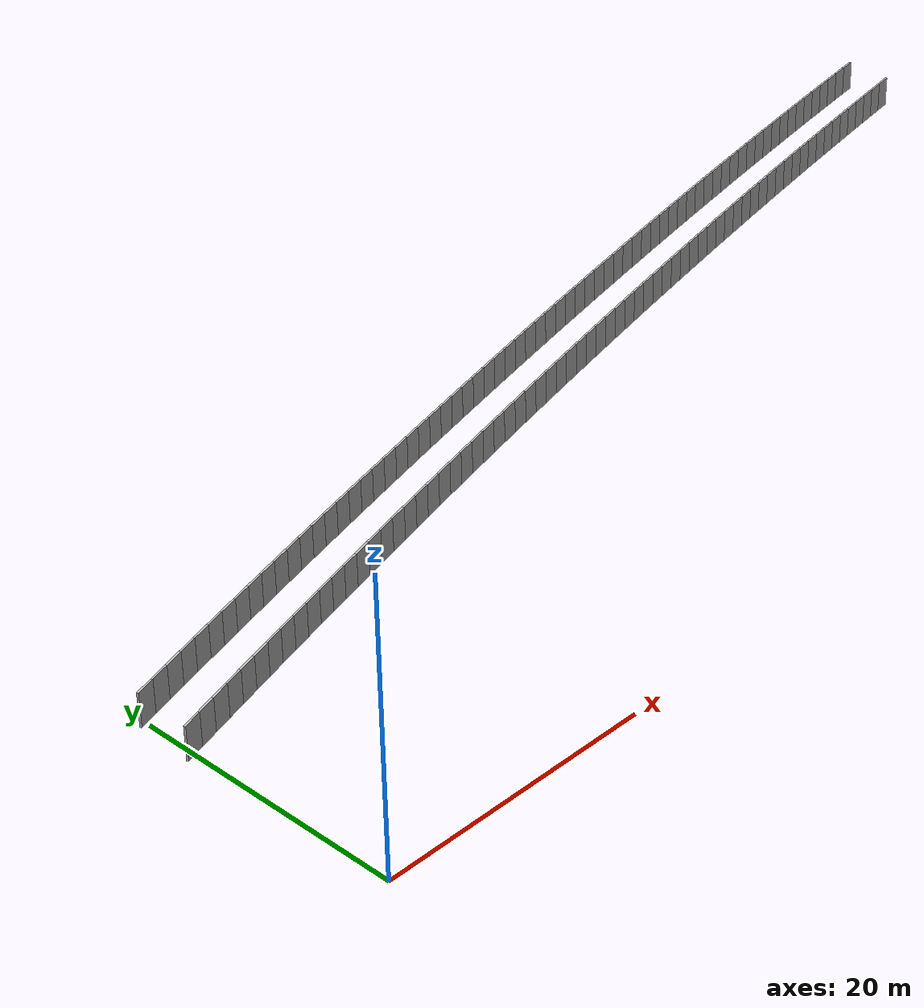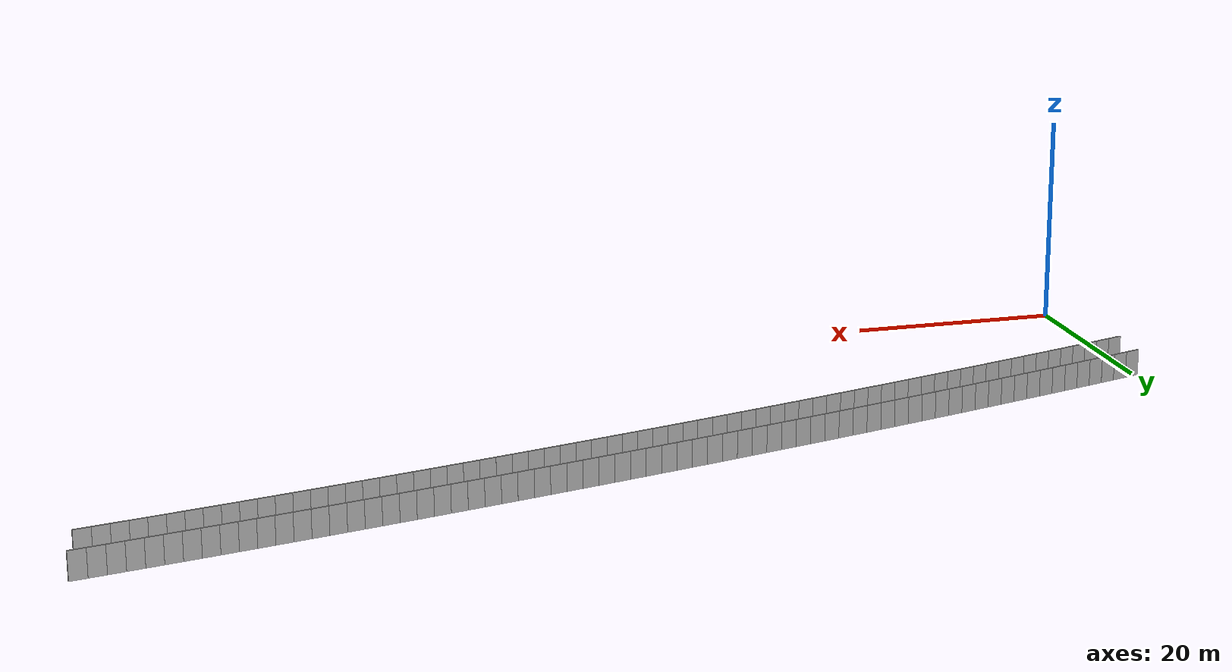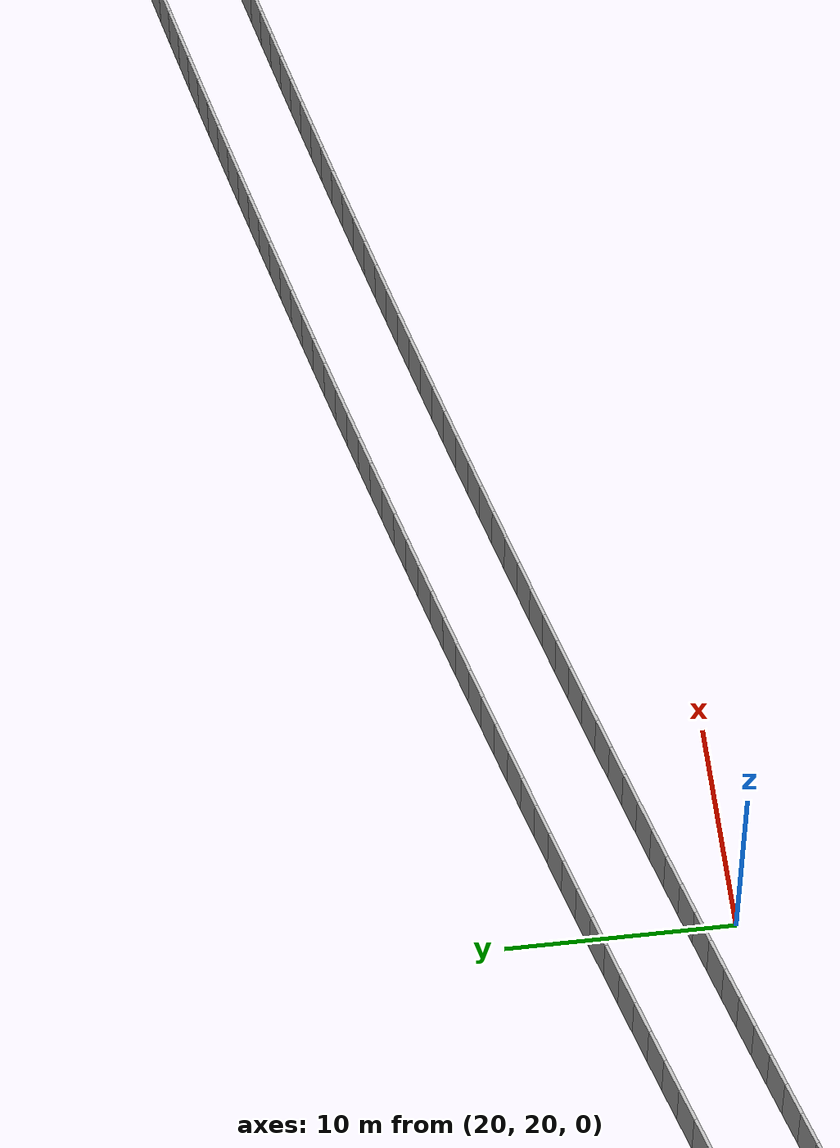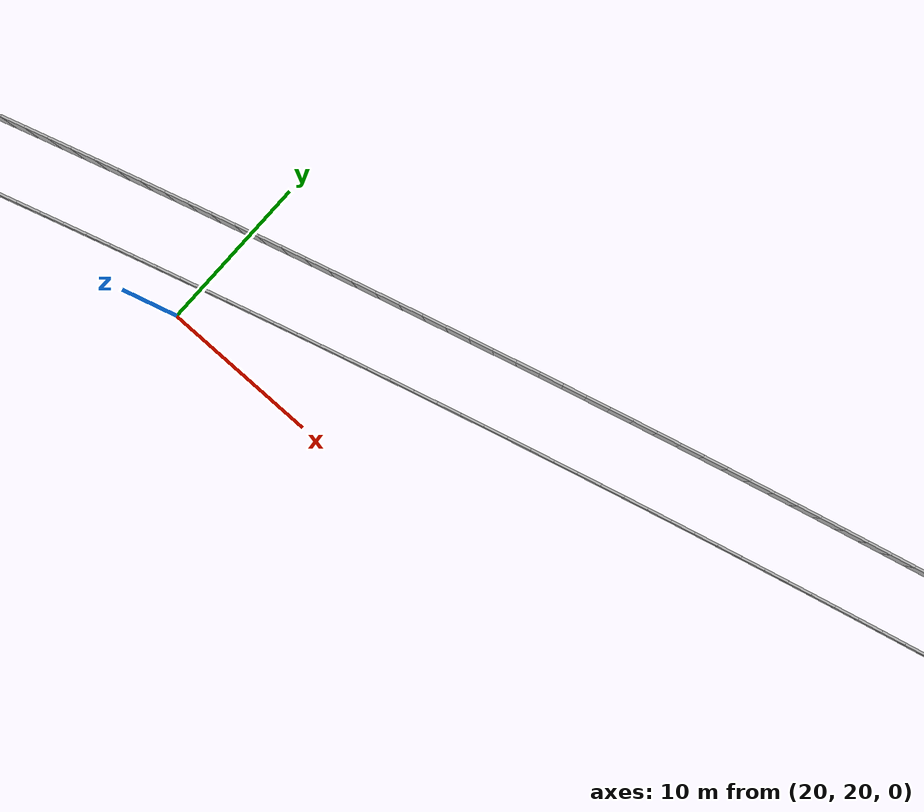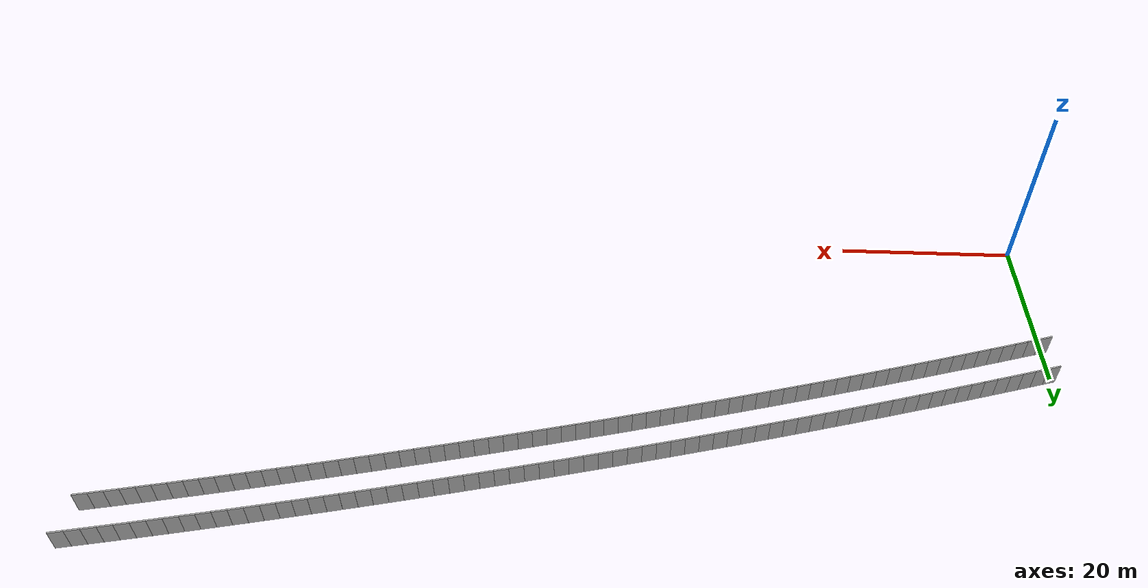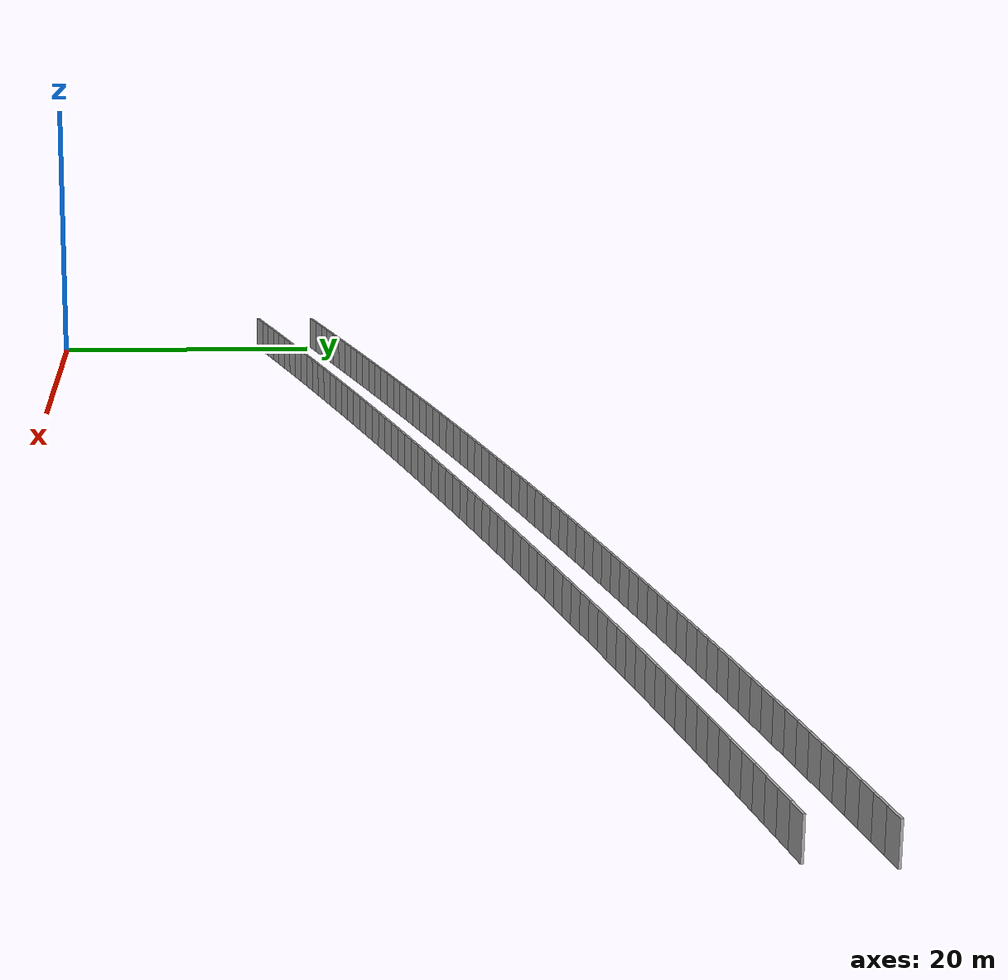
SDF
<?xml version="1.0" ?>
<sdf version="1.6">
  <model name="sps_0923">
    <pose frame="">0 0 0 0 -0 0</pose>
    <static>1</static>
    <self_collide>0</self_collide>
    <allow_auto_disable>0</allow_auto_disable>
    <link name="Wall3027">
      <kinematic>0</kinematic>
      <gravity>1</gravity>
      <self_collide>0</self_collide>
      <collision name="collision">
        <geometry>
          <box>
            <size>1.49635 0.15 2.5</size>
          </box>
        </geometry>
        <pose frame="">0 0 0 0 -0 0</pose>
      </collision>
      <visual name="visual">
        <geometry>
          <box>
            <size>1.49635 0.15 2.5</size>
          </box>
        </geometry>
        <pose frame="">0 0 0 0 -0 0</pose>
        <cast_shadows>1</cast_shadows>
        <transparency>0.0</transparency>
      </visual>
      <pose frame="">98.6193 41.263 1.25 0 0 -2.94586</pose>
    </link>
    <link name="Wall3028">
      <kinematic>0</kinematic>
      <gravity>1</gravity>
      <self_collide>0</self_collide>
      <collision name="collision">
        <geometry>
          <box>
            <size>1.49668 0.15 2.5</size>
          </box>
        </geometry>
        <pose frame="">0 0 0 0 -0 0</pose>
      </collision>
      <visual name="visual">
        <geometry>
          <box>
            <size>1.49668 0.15 2.5</size>
          </box>
        </geometry>
        <pose frame="">0 0 0 0 -0 0</pose>
        <cast_shadows>1</cast_shadows>
        <transparency>0.0</transparency>
      </visual>
      <pose frame="">97.1517 40.9707 1.25 0 0 -2.94412</pose>
    </link>
    <link name="Wall3029">
      <kinematic>0</kinematic>
      <gravity>1</gravity>
      <self_collide>0</self_collide>
      <collision name="collision">
        <geometry>
          <box>
            <size>1.49624 0.15 2.5</size>
          </box>
        </geometry>
        <pose frame="">0 0 0 0 -0 0</pose>
      </collision>
      <visual name="visual">
        <geometry>
          <box>
            <size>1.49624 0.15 2.5</size>
          </box>
        </geometry>
        <pose frame="">0 0 0 0 -0 0</pose>
        <cast_shadows>1</cast_shadows>
        <transparency>0.0</transparency>
      </visual>
      <pose frame="">95.6845 40.6762 1.25 0 0 -2.94289</pose>
    </link>
    <link name="Wall3030">
      <kinematic>0</kinematic>
      <gravity>1</gravity>
      <self_collide>0</self_collide>
      <collision name="collision">
        <geometry>
          <box>
            <size>1.49663 0.15 2.5</size>
          </box>
        </geometry>
        <pose frame="">0 0 0 0 -0 0</pose>
      </collision>
      <visual name="visual">
        <geometry>
          <box>
            <size>1.49663 0.15 2.5</size>
          </box>
        </geometry>
        <pose frame="">0 0 0 0 -0 0</pose>
        <cast_shadows>1</cast_shadows>
        <transparency>0.0</transparency>
      </visual>
      <pose frame="">94.2178 40.3794 1.25 0 0 -2.94099</pose>
    </link>
    <link name="Wall3031">
      <kinematic>0</kinematic>
      <gravity>1</gravity>
      <self_collide>0</self_collide>
      <collision name="collision">
        <geometry>
          <box>
            <size>1.49647 0.15 2.5</size>
          </box>
        </geometry>
        <pose frame="">0 0 0 0 -0 0</pose>
      </collision>
      <visual name="visual">
        <geometry>
          <box>
            <size>1.49647 0.15 2.5</size>
          </box>
        </geometry>
        <pose frame="">0 0 0 0 -0 0</pose>
        <cast_shadows>1</cast_shadows>
        <transparency>0.0</transparency>
      </visual>
      <pose frame="">92.7515 40.0801 1.25 0 0 -2.93947</pose>
    </link>
    <link name="Wall3032">
      <kinematic>0</kinematic>
      <gravity>1</gravity>
      <self_collide>0</self_collide>
      <collision name="collision">
        <geometry>
          <box>
            <size>1.49653 0.15 2.5</size>
          </box>
        </geometry>
        <pose frame="">0 0 0 0 -0 0</pose>
      </collision>
      <visual name="visual">
        <geometry>
          <box>
            <size>1.49653 0.15 2.5</size>
          </box>
        </geometry>
        <pose frame="">0 0 0 0 -0 0</pose>
        <cast_shadows>1</cast_shadows>
        <transparency>0.0</transparency>
      </visual>
      <pose frame="">91.2857 39.7785 1.25 0 0 -2.93785</pose>
    </link>
    <link name="Wall3033">
      <kinematic>0</kinematic>
      <gravity>1</gravity>
      <self_collide>0</self_collide>
      <collision name="collision">
        <geometry>
          <box>
            <size>1.49647 0.15 2.5</size>
          </box>
        </geometry>
        <pose frame="">0 0 0 0 -0 0</pose>
      </collision>
      <visual name="visual">
        <geometry>
          <box>
            <size>1.49647 0.15 2.5</size>
          </box>
        </geometry>
        <pose frame="">0 0 0 0 -0 0</pose>
        <cast_shadows>1</cast_shadows>
        <transparency>0.0</transparency>
      </visual>
      <pose frame="">89.8204 39.4745 1.25 0 0 -2.93622</pose>
    </link>
    <link name="Wall3034">
      <kinematic>0</kinematic>
      <gravity>1</gravity>
      <self_collide>0</self_collide>
      <collision name="collision">
        <geometry>
          <box>
            <size>1.49652 0.15 2.5</size>
          </box>
        </geometry>
        <pose frame="">0 0 0 0 -0 0</pose>
      </collision>
      <visual name="visual">
        <geometry>
          <box>
            <size>1.49652 0.15 2.5</size>
          </box>
        </geometry>
        <pose frame="">0 0 0 0 -0 0</pose>
        <cast_shadows>1</cast_shadows>
        <transparency>0.0</transparency>
      </visual>
      <pose frame="">88.3556 39.1682 1.25 0 0 -2.93469</pose>
    </link>
    <link name="Wall3035">
      <kinematic>0</kinematic>
      <gravity>1</gravity>
      <self_collide>0</self_collide>
      <collision name="collision">
        <geometry>
          <box>
            <size>1.49636 0.15 2.5</size>
          </box>
        </geometry>
        <pose frame="">0 0 0 0 -0 0</pose>
      </collision>
      <visual name="visual">
        <geometry>
          <box>
            <size>1.49636 0.15 2.5</size>
          </box>
        </geometry>
        <pose frame="">0 0 0 0 -0 0</pose>
        <cast_shadows>1</cast_shadows>
        <transparency>0.0</transparency>
      </visual>
      <pose frame="">86.8913 38.8597 1.25 0 0 -2.93321</pose>
    </link>
    <link name="Wall3036">
      <kinematic>0</kinematic>
      <gravity>1</gravity>
      <self_collide>0</self_collide>
      <collision name="collision">
        <geometry>
          <box>
            <size>1.49651 0.15 2.5</size>
          </box>
        </geometry>
        <pose frame="">0 0 0 0 -0 0</pose>
      </collision>
      <visual name="visual">
        <geometry>
          <box>
            <size>1.49651 0.15 2.5</size>
          </box>
        </geometry>
        <pose frame="">0 0 0 0 -0 0</pose>
        <cast_shadows>1</cast_shadows>
        <transparency>0.0</transparency>
      </visual>
      <pose frame="">85.4275 38.5489 1.25 0 0 -2.93156</pose>
    </link>
    <link name="Wall3037">
      <kinematic>0</kinematic>
      <gravity>1</gravity>
      <self_collide>0</self_collide>
      <collision name="collision">
        <geometry>
          <box>
            <size>1.49659 0.15 2.5</size>
          </box>
        </geometry>
        <pose frame="">0 0 0 0 -0 0</pose>
      </collision>
      <visual name="visual">
        <geometry>
          <box>
            <size>1.49659 0.15 2.5</size>
          </box>
        </geometry>
        <pose frame="">0 0 0 0 -0 0</pose>
        <cast_shadows>1</cast_shadows>
        <transparency>0.0</transparency>
      </visual>
      <pose frame="">83.964 38.2357 1.25 0 0 -2.92994</pose>
    </link>
    <link name="Wall3038">
      <kinematic>0</kinematic>
      <gravity>1</gravity>
      <self_collide>0</self_collide>
      <collision name="collision">
        <geometry>
          <box>
            <size>1.49651 0.15 2.5</size>
          </box>
        </geometry>
        <pose frame="">0 0 0 0 -0 0</pose>
      </collision>
      <visual name="visual">
        <geometry>
          <box>
            <size>1.49651 0.15 2.5</size>
          </box>
        </geometry>
        <pose frame="">0 0 0 0 -0 0</pose>
        <cast_shadows>1</cast_shadows>
        <transparency>0.0</transparency>
      </visual>
      <pose frame="">82.5012 37.9201 1.25 0 0 -2.92826</pose>
    </link>
    <link name="Wall3039">
      <kinematic>0</kinematic>
      <gravity>1</gravity>
      <self_collide>0</self_collide>
      <collision name="collision">
        <geometry>
          <box>
            <size>1.49661 0.15 2.5</size>
          </box>
        </geometry>
        <pose frame="">0 0 0 0 -0 0</pose>
      </collision>
      <visual name="visual">
        <geometry>
          <box>
            <size>1.49661 0.15 2.5</size>
          </box>
        </geometry>
        <pose frame="">0 0 0 0 -0 0</pose>
        <cast_shadows>1</cast_shadows>
        <transparency>0.0</transparency>
      </visual>
      <pose frame="">81.0387 37.6022 1.25 0 0 -2.92682</pose>
    </link>
    <link name="Wall3040">
      <kinematic>0</kinematic>
      <gravity>1</gravity>
      <self_collide>0</self_collide>
      <collision name="collision">
        <geometry>
          <box>
            <size>1.49649 0.15 2.5</size>
          </box>
        </geometry>
        <pose frame="">0 0 0 0 -0 0</pose>
      </collision>
      <visual name="visual">
        <geometry>
          <box>
            <size>1.49649 0.15 2.5</size>
          </box>
        </geometry>
        <pose frame="">0 0 0 0 -0 0</pose>
        <cast_shadows>1</cast_shadows>
        <transparency>0.0</transparency>
      </visual>
      <pose frame="">79.5768 37.2821 1.25 0 0 -2.92526</pose>
    </link>
    <link name="Wall3041">
      <kinematic>0</kinematic>
      <gravity>1</gravity>
      <self_collide>0</self_collide>
      <collision name="collision">
        <geometry>
          <box>
            <size>1.49641 0.15 2.5</size>
          </box>
        </geometry>
        <pose frame="">0 0 0 0 -0 0</pose>
      </collision>
      <visual name="visual">
        <geometry>
          <box>
            <size>1.49641 0.15 2.5</size>
          </box>
        </geometry>
        <pose frame="">0 0 0 0 -0 0</pose>
        <cast_shadows>1</cast_shadows>
        <transparency>0.0</transparency>
      </visual>
      <pose frame="">78.1155 36.9597 1.25 0 0 -2.92361</pose>
    </link>
    <link name="Wall3042">
      <kinematic>0</kinematic>
      <gravity>1</gravity>
      <self_collide>0</self_collide>
      <collision name="collision">
        <geometry>
          <box>
            <size>1.49651 0.15 2.5</size>
          </box>
        </geometry>
        <pose frame="">0 0 0 0 -0 0</pose>
      </collision>
      <visual name="visual">
        <geometry>
          <box>
            <size>1.49651 0.15 2.5</size>
          </box>
        </geometry>
        <pose frame="">0 0 0 0 -0 0</pose>
        <cast_shadows>1</cast_shadows>
        <transparency>0.0</transparency>
      </visual>
      <pose frame="">76.6547 36.6349 1.25 0 0 -2.922</pose>
    </link>
    <link name="Wall3043">
      <kinematic>0</kinematic>
      <gravity>1</gravity>
      <self_collide>0</self_collide>
      <collision name="collision">
        <geometry>
          <box>
            <size>1.49645 0.15 2.5</size>
          </box>
        </geometry>
        <pose frame="">0 0 0 0 -0 0</pose>
      </collision>
      <visual name="visual">
        <geometry>
          <box>
            <size>1.49645 0.15 2.5</size>
          </box>
        </geometry>
        <pose frame="">0 0 0 0 -0 0</pose>
        <cast_shadows>1</cast_shadows>
        <transparency>0.0</transparency>
      </visual>
      <pose frame="">75.1944 36.3078 1.25 0 0 -2.92049</pose>
    </link>
    <link name="Wall3044">
      <kinematic>0</kinematic>
      <gravity>1</gravity>
      <self_collide>0</self_collide>
      <collision name="collision">
        <geometry>
          <box>
            <size>1.49657 0.15 2.5</size>
          </box>
        </geometry>
        <pose frame="">0 0 0 0 -0 0</pose>
      </collision>
      <visual name="visual">
        <geometry>
          <box>
            <size>1.49657 0.15 2.5</size>
          </box>
        </geometry>
        <pose frame="">0 0 0 0 -0 0</pose>
        <cast_shadows>1</cast_shadows>
        <transparency>0.0</transparency>
      </visual>
      <pose frame="">73.7346 35.9784 1.25 0 0 -2.91883</pose>
    </link>
    <link name="Wall3045">
      <kinematic>0</kinematic>
      <gravity>1</gravity>
      <self_collide>0</self_collide>
      <collision name="collision">
        <geometry>
          <box>
            <size>1.49637 0.15 2.5</size>
          </box>
        </geometry>
        <pose frame="">0 0 0 0 -0 0</pose>
      </collision>
      <visual name="visual">
        <geometry>
          <box>
            <size>1.49637 0.15 2.5</size>
          </box>
        </geometry>
        <pose frame="">0 0 0 0 -0 0</pose>
        <cast_shadows>1</cast_shadows>
        <transparency>0.0</transparency>
      </visual>
      <pose frame="">72.2754 35.6469 1.25 0 0 -2.91759</pose>
    </link>
    <link name="Wall3046">
      <kinematic>0</kinematic>
      <gravity>1</gravity>
      <self_collide>0</self_collide>
      <collision name="collision">
        <geometry>
          <box>
            <size>1.49644 0.15 2.5</size>
          </box>
        </geometry>
        <pose frame="">0 0 0 0 -0 0</pose>
      </collision>
      <visual name="visual">
        <geometry>
          <box>
            <size>1.49644 0.15 2.5</size>
          </box>
        </geometry>
        <pose frame="">0 0 0 0 -0 0</pose>
        <cast_shadows>1</cast_shadows>
        <transparency>0.0</transparency>
      </visual>
      <pose frame="">70.8167 35.313 1.25 0 0 -2.91555</pose>
    </link>
    <link name="Wall3047">
      <kinematic>0</kinematic>
      <gravity>1</gravity>
      <self_collide>0</self_collide>
      <collision name="collision">
        <geometry>
          <box>
            <size>1.49654 0.15 2.5</size>
          </box>
        </geometry>
        <pose frame="">0 0 0 0 -0 0</pose>
      </collision>
      <visual name="visual">
        <geometry>
          <box>
            <size>1.49654 0.15 2.5</size>
          </box>
        </geometry>
        <pose frame="">0 0 0 0 -0 0</pose>
        <cast_shadows>1</cast_shadows>
        <transparency>0.0</transparency>
      </visual>
      <pose frame="">69.3585 34.9766 1.25 0 0 -2.91418</pose>
    </link>
    <link name="Wall3048">
      <kinematic>0</kinematic>
      <gravity>1</gravity>
      <self_collide>0</self_collide>
      <collision name="collision">
        <geometry>
          <box>
            <size>1.49652 0.15 2.5</size>
          </box>
        </geometry>
        <pose frame="">0 0 0 0 -0 0</pose>
      </collision>
      <visual name="visual">
        <geometry>
          <box>
            <size>1.49652 0.15 2.5</size>
          </box>
        </geometry>
        <pose frame="">0 0 0 0 -0 0</pose>
        <cast_shadows>1</cast_shadows>
        <transparency>0.0</transparency>
      </visual>
      <pose frame="">67.9008 34.6379 1.25 0 0 -2.91242</pose>
    </link>
    <link name="Wall3049">
      <kinematic>0</kinematic>
      <gravity>1</gravity>
      <self_collide>0</self_collide>
      <collision name="collision">
        <geometry>
          <box>
            <size>1.49646 0.15 2.5</size>
          </box>
        </geometry>
        <pose frame="">0 0 0 0 -0 0</pose>
      </collision>
      <visual name="visual">
        <geometry>
          <box>
            <size>1.49646 0.15 2.5</size>
          </box>
        </geometry>
        <pose frame="">0 0 0 0 -0 0</pose>
        <cast_shadows>1</cast_shadows>
        <transparency>0.0</transparency>
      </visual>
      <pose frame="">66.4437 34.2969 1.25 0 0 -2.91099</pose>
    </link>
    <link name="Wall3050">
      <kinematic>0</kinematic>
      <gravity>1</gravity>
      <self_collide>0</self_collide>
      <collision name="collision">
        <geometry>
          <box>
            <size>1.49652 0.15 2.5</size>
          </box>
        </geometry>
        <pose frame="">0 0 0 0 -0 0</pose>
      </collision>
      <visual name="visual">
        <geometry>
          <box>
            <size>1.49652 0.15 2.5</size>
          </box>
        </geometry>
        <pose frame="">0 0 0 0 -0 0</pose>
        <cast_shadows>1</cast_shadows>
        <transparency>0.0</transparency>
      </visual>
      <pose frame="">64.9871 33.9537 1.25 0 0 -2.9094</pose>
    </link>
    <link name="Wall3051">
      <kinematic>0</kinematic>
      <gravity>1</gravity>
      <self_collide>0</self_collide>
      <collision name="collision">
        <geometry>
          <box>
            <size>1.49637 0.15 2.5</size>
          </box>
        </geometry>
        <pose frame="">0 0 0 0 -0 0</pose>
      </collision>
      <visual name="visual">
        <geometry>
          <box>
            <size>1.49637 0.15 2.5</size>
          </box>
        </geometry>
        <pose frame="">0 0 0 0 -0 0</pose>
        <cast_shadows>1</cast_shadows>
        <transparency>0.0</transparency>
      </visual>
      <pose frame="">63.5311 33.6081 1.25 0 0 -2.9077</pose>
    </link>
    <link name="Wall3052">
      <kinematic>0</kinematic>
      <gravity>1</gravity>
      <self_collide>0</self_collide>
      <collision name="collision">
        <geometry>
          <box>
            <size>1.49664 0.15 2.5</size>
          </box>
        </geometry>
        <pose frame="">0 0 0 0 -0 0</pose>
      </collision>
      <visual name="visual">
        <geometry>
          <box>
            <size>1.49664 0.15 2.5</size>
          </box>
        </geometry>
        <pose frame="">0 0 0 0 -0 0</pose>
        <cast_shadows>1</cast_shadows>
        <transparency>0.0</transparency>
      </visual>
      <pose frame="">62.0756 33.2602 1.25 0 0 -2.90624</pose>
    </link>
    <link name="Wall3053">
      <kinematic>0</kinematic>
      <gravity>1</gravity>
      <self_collide>0</self_collide>
      <collision name="collision">
        <geometry>
          <box>
            <size>1.49668 0.15 2.5</size>
          </box>
        </geometry>
        <pose frame="">0 0 0 0 -0 0</pose>
      </collision>
      <visual name="visual">
        <geometry>
          <box>
            <size>1.49668 0.15 2.5</size>
          </box>
        </geometry>
        <pose frame="">0 0 0 0 -0 0</pose>
        <cast_shadows>1</cast_shadows>
        <transparency>0.0</transparency>
      </visual>
      <pose frame="">60.6204 32.91 1.25 0 0 -2.90457</pose>
    </link>
    <link name="Wall3054">
      <kinematic>0</kinematic>
      <gravity>1</gravity>
      <self_collide>0</self_collide>
      <collision name="collision">
        <geometry>
          <box>
            <size>1.49635 0.15 2.5</size>
          </box>
        </geometry>
        <pose frame="">0 0 0 0 -0 0</pose>
      </collision>
      <visual name="visual">
        <geometry>
          <box>
            <size>1.49635 0.15 2.5</size>
          </box>
        </geometry>
        <pose frame="">0 0 0 0 -0 0</pose>
        <cast_shadows>1</cast_shadows>
        <transparency>0.0</transparency>
      </visual>
      <pose frame="">59.166 32.5575 1.25 0 0 -2.90304</pose>
    </link>
    <link name="Wall3055">
      <kinematic>0</kinematic>
      <gravity>1</gravity>
      <self_collide>0</self_collide>
      <collision name="collision">
        <geometry>
          <box>
            <size>1.49658 0.15 2.5</size>
          </box>
        </geometry>
        <pose frame="">0 0 0 0 -0 0</pose>
      </collision>
      <visual name="visual">
        <geometry>
          <box>
            <size>1.49658 0.15 2.5</size>
          </box>
        </geometry>
        <pose frame="">0 0 0 0 -0 0</pose>
        <cast_shadows>1</cast_shadows>
        <transparency>0.0</transparency>
      </visual>
      <pose frame="">57.7122 32.2027 1.25 0 0 -2.9014</pose>
    </link>
    <link name="Wall3056">
      <kinematic>0</kinematic>
      <gravity>1</gravity>
      <self_collide>0</self_collide>
      <collision name="collision">
        <geometry>
          <box>
            <size>1.49649 0.15 2.5</size>
          </box>
        </geometry>
        <pose frame="">0 0 0 0 -0 0</pose>
      </collision>
      <visual name="visual">
        <geometry>
          <box>
            <size>1.49649 0.15 2.5</size>
          </box>
        </geometry>
        <pose frame="">0 0 0 0 -0 0</pose>
        <cast_shadows>1</cast_shadows>
        <transparency>0.0</transparency>
      </visual>
      <pose frame="">56.2589 31.8456 1.25 0 0 -2.89992</pose>
    </link>
    <link name="Wall3057">
      <kinematic>0</kinematic>
      <gravity>1</gravity>
      <self_collide>0</self_collide>
      <collision name="collision">
        <geometry>
          <box>
            <size>1.49649 0.15 2.5</size>
          </box>
        </geometry>
        <pose frame="">0 0 0 0 -0 0</pose>
      </collision>
      <visual name="visual">
        <geometry>
          <box>
            <size>1.49649 0.15 2.5</size>
          </box>
        </geometry>
        <pose frame="">0 0 0 0 -0 0</pose>
        <cast_shadows>1</cast_shadows>
        <transparency>0.0</transparency>
      </visual>
      <pose frame="">54.8062 31.4862 1.25 0 0 -2.89824</pose>
    </link>
    <link name="Wall3058">
      <kinematic>0</kinematic>
      <gravity>1</gravity>
      <self_collide>0</self_collide>
      <collision name="collision">
        <geometry>
          <box>
            <size>1.49644 0.15 2.5</size>
          </box>
        </geometry>
        <pose frame="">0 0 0 0 -0 0</pose>
      </collision>
      <visual name="visual">
        <geometry>
          <box>
            <size>1.49644 0.15 2.5</size>
          </box>
        </geometry>
        <pose frame="">0 0 0 0 -0 0</pose>
        <cast_shadows>1</cast_shadows>
        <transparency>0.0</transparency>
      </visual>
      <pose frame="">53.3541 31.1245 1.25 0 0 -2.89667</pose>
    </link>
    <link name="Wall3059">
      <kinematic>0</kinematic>
      <gravity>1</gravity>
      <self_collide>0</self_collide>
      <collision name="collision">
        <geometry>
          <box>
            <size>1.49641 0.15 2.5</size>
          </box>
        </geometry>
        <pose frame="">0 0 0 0 -0 0</pose>
      </collision>
      <visual name="visual">
        <geometry>
          <box>
            <size>1.49641 0.15 2.5</size>
          </box>
        </geometry>
        <pose frame="">0 0 0 0 -0 0</pose>
        <cast_shadows>1</cast_shadows>
        <transparency>0.0</transparency>
      </visual>
      <pose frame="">51.9027 30.7605 1.25 0 0 -2.89507</pose>
    </link>
    <link name="Wall3060">
      <kinematic>0</kinematic>
      <gravity>1</gravity>
      <self_collide>0</self_collide>
      <collision name="collision">
        <geometry>
          <box>
            <size>1.49637 0.15 2.5</size>
          </box>
        </geometry>
        <pose frame="">0 0 0 0 -0 0</pose>
      </collision>
      <visual name="visual">
        <geometry>
          <box>
            <size>1.49637 0.15 2.5</size>
          </box>
        </geometry>
        <pose frame="">0 0 0 0 -0 0</pose>
        <cast_shadows>1</cast_shadows>
        <transparency>0.0</transparency>
      </visual>
      <pose frame="">50.4518 30.3943 1.25 0 0 -2.89368</pose>
    </link>
    <link name="Wall3061">
      <kinematic>0</kinematic>
      <gravity>1</gravity>
      <self_collide>0</self_collide>
      <collision name="collision">
        <geometry>
          <box>
            <size>1.49661 0.15 2.5</size>
          </box>
        </geometry>
        <pose frame="">0 0 0 0 -0 0</pose>
      </collision>
      <visual name="visual">
        <geometry>
          <box>
            <size>1.49661 0.15 2.5</size>
          </box>
        </geometry>
        <pose frame="">0 0 0 0 -0 0</pose>
        <cast_shadows>1</cast_shadows>
        <transparency>0.0</transparency>
      </visual>
      <pose frame="">49.0014 30.0258 1.25 0 0 -2.89191</pose>
    </link>
    <link name="Wall3062">
      <kinematic>0</kinematic>
      <gravity>1</gravity>
      <self_collide>0</self_collide>
      <collision name="collision">
        <geometry>
          <box>
            <size>1.49638 0.15 2.5</size>
          </box>
        </geometry>
        <pose frame="">0 0 0 0 -0 0</pose>
      </collision>
      <visual name="visual">
        <geometry>
          <box>
            <size>1.49638 0.15 2.5</size>
          </box>
        </geometry>
        <pose frame="">0 0 0 0 -0 0</pose>
        <cast_shadows>1</cast_shadows>
        <transparency>0.0</transparency>
      </visual>
      <pose frame="">47.5516 29.6549 1.25 0 0 -2.89035</pose>
    </link>
    <link name="Wall3063">
      <kinematic>0</kinematic>
      <gravity>1</gravity>
      <self_collide>0</self_collide>
      <collision name="collision">
        <geometry>
          <box>
            <size>1.49662 0.15 2.5</size>
          </box>
        </geometry>
        <pose frame="">0 0 0 0 -0 0</pose>
      </collision>
      <visual name="visual">
        <geometry>
          <box>
            <size>1.49662 0.15 2.5</size>
          </box>
        </geometry>
        <pose frame="">0 0 0 0 -0 0</pose>
        <cast_shadows>1</cast_shadows>
        <transparency>0.0</transparency>
      </visual>
      <pose frame="">46.1023 29.2817 1.25 0 0 -2.88875</pose>
    </link>
    <link name="Wall3064">
      <kinematic>0</kinematic>
      <gravity>1</gravity>
      <self_collide>0</self_collide>
      <collision name="collision">
        <geometry>
          <box>
            <size>1.49634 0.15 2.5</size>
          </box>
        </geometry>
        <pose frame="">0 0 0 0 -0 0</pose>
      </collision>
      <visual name="visual">
        <geometry>
          <box>
            <size>1.49634 0.15 2.5</size>
          </box>
        </geometry>
        <pose frame="">0 0 0 0 -0 0</pose>
        <cast_shadows>1</cast_shadows>
        <transparency>0.0</transparency>
      </visual>
      <pose frame="">44.6537 28.9062 1.25 0 0 -2.88719</pose>
    </link>
    <link name="Wall3065">
      <kinematic>0</kinematic>
      <gravity>1</gravity>
      <self_collide>0</self_collide>
      <collision name="collision">
        <geometry>
          <box>
            <size>1.49661 0.15 2.5</size>
          </box>
        </geometry>
        <pose frame="">0 0 0 0 -0 0</pose>
      </collision>
      <visual name="visual">
        <geometry>
          <box>
            <size>1.49661 0.15 2.5</size>
          </box>
        </geometry>
        <pose frame="">0 0 0 0 -0 0</pose>
        <cast_shadows>1</cast_shadows>
        <transparency>0.0</transparency>
      </visual>
      <pose frame="">43.2057 28.5284 1.25 0 0 -2.88555</pose>
    </link>
    <link name="Wall3066">
      <kinematic>0</kinematic>
      <gravity>1</gravity>
      <self_collide>0</self_collide>
      <collision name="collision">
        <geometry>
          <box>
            <size>1.49656 0.15 2.5</size>
          </box>
        </geometry>
        <pose frame="">0 0 0 0 -0 0</pose>
      </collision>
      <visual name="visual">
        <geometry>
          <box>
            <size>1.49656 0.15 2.5</size>
          </box>
        </geometry>
        <pose frame="">0 0 0 0 -0 0</pose>
        <cast_shadows>1</cast_shadows>
        <transparency>0.0</transparency>
      </visual>
      <pose frame="">41.7582 28.1483 1.25 0 0 -2.88406</pose>
    </link>
    <link name="Wall3067">
      <kinematic>0</kinematic>
      <gravity>1</gravity>
      <self_collide>0</self_collide>
      <collision name="collision">
        <geometry>
          <box>
            <size>1.49659 0.15 2.5</size>
          </box>
        </geometry>
        <pose frame="">0 0 0 0 -0 0</pose>
      </collision>
      <visual name="visual">
        <geometry>
          <box>
            <size>1.49659 0.15 2.5</size>
          </box>
        </geometry>
        <pose frame="">0 0 0 0 -0 0</pose>
        <cast_shadows>1</cast_shadows>
        <transparency>0.0</transparency>
      </visual>
      <pose frame="">40.3113 27.7659 1.25 0 0 -2.88238</pose>
    </link>
    <link name="Wall3068">
      <kinematic>0</kinematic>
      <gravity>1</gravity>
      <self_collide>0</self_collide>
      <collision name="collision">
        <geometry>
          <box>
            <size>1.49639 0.15 2.5</size>
          </box>
        </geometry>
        <pose frame="">0 0 0 0 -0 0</pose>
      </collision>
      <visual name="visual">
        <geometry>
          <box>
            <size>1.49639 0.15 2.5</size>
          </box>
        </geometry>
        <pose frame="">0 0 0 0 -0 0</pose>
        <cast_shadows>1</cast_shadows>
        <transparency>0.0</transparency>
      </visual>
      <pose frame="">38.8651 27.3812 1.25 0 0 -2.88082</pose>
    </link>
    <link name="Wall3069">
      <kinematic>0</kinematic>
      <gravity>1</gravity>
      <self_collide>0</self_collide>
      <collision name="collision">
        <geometry>
          <box>
            <size>1.49655 0.15 2.5</size>
          </box>
        </geometry>
        <pose frame="">0 0 0 0 -0 0</pose>
      </collision>
      <visual name="visual">
        <geometry>
          <box>
            <size>1.49655 0.15 2.5</size>
          </box>
        </geometry>
        <pose frame="">0 0 0 0 -0 0</pose>
        <cast_shadows>1</cast_shadows>
        <transparency>0.0</transparency>
      </visual>
      <pose frame="">37.4195 26.9943 1.25 0 0 -2.87933</pose>
    </link>
    <link name="Wall3070">
      <kinematic>0</kinematic>
      <gravity>1</gravity>
      <self_collide>0</self_collide>
      <collision name="collision">
        <geometry>
          <box>
            <size>1.49641 0.15 2.5</size>
          </box>
        </geometry>
        <pose frame="">0 0 0 0 -0 0</pose>
      </collision>
      <visual name="visual">
        <geometry>
          <box>
            <size>1.49641 0.15 2.5</size>
          </box>
        </geometry>
        <pose frame="">0 0 0 0 -0 0</pose>
        <cast_shadows>1</cast_shadows>
        <transparency>0.0</transparency>
      </visual>
      <pose frame="">35.9746 26.6051 1.25 0 0 -2.87762</pose>
    </link>
    <link name="Wall3071">
      <kinematic>0</kinematic>
      <gravity>1</gravity>
      <self_collide>0</self_collide>
      <collision name="collision">
        <geometry>
          <box>
            <size>1.49644 0.15 2.5</size>
          </box>
        </geometry>
        <pose frame="">0 0 0 0 -0 0</pose>
      </collision>
      <visual name="visual">
        <geometry>
          <box>
            <size>1.49644 0.15 2.5</size>
          </box>
        </geometry>
        <pose frame="">0 0 0 0 -0 0</pose>
        <cast_shadows>1</cast_shadows>
        <transparency>0.0</transparency>
      </visual>
      <pose frame="">34.5303 26.2136 1.25 0 0 -2.87615</pose>
    </link>
    <link name="Wall3072">
      <kinematic>0</kinematic>
      <gravity>1</gravity>
      <self_collide>0</self_collide>
      <collision name="collision">
        <geometry>
          <box>
            <size>1.4965 0.15 2.5</size>
          </box>
        </geometry>
        <pose frame="">0 0 0 0 -0 0</pose>
      </collision>
      <visual name="visual">
        <geometry>
          <box>
            <size>1.4965 0.15 2.5</size>
          </box>
        </geometry>
        <pose frame="">0 0 0 0 -0 0</pose>
        <cast_shadows>1</cast_shadows>
        <transparency>0.0</transparency>
      </visual>
      <pose frame="">33.0865 25.8198 1.25 0 0 -2.87446</pose>
    </link>
    <link name="Wall3073">
      <kinematic>0</kinematic>
      <gravity>1</gravity>
      <self_collide>0</self_collide>
      <collision name="collision">
        <geometry>
          <box>
            <size>1.49672 0.15 2.5</size>
          </box>
        </geometry>
        <pose frame="">0 0 0 0 -0 0</pose>
      </collision>
      <visual name="visual">
        <geometry>
          <box>
            <size>1.49672 0.15 2.5</size>
          </box>
        </geometry>
        <pose frame="">0 0 0 0 -0 0</pose>
        <cast_shadows>1</cast_shadows>
        <transparency>0.0</transparency>
      </visual>
      <pose frame="">31.6433 25.4236 1.25 0 0 -2.87285</pose>
    </link>
    <link name="Wall3074">
      <kinematic>0</kinematic>
      <gravity>1</gravity>
      <self_collide>0</self_collide>
      <collision name="collision">
        <geometry>
          <box>
            <size>1.49654 0.15 2.5</size>
          </box>
        </geometry>
        <pose frame="">0 0 0 0 -0 0</pose>
      </collision>
      <visual name="visual">
        <geometry>
          <box>
            <size>1.49654 0.15 2.5</size>
          </box>
        </geometry>
        <pose frame="">0 0 0 0 -0 0</pose>
        <cast_shadows>1</cast_shadows>
        <transparency>0.0</transparency>
      </visual>
      <pose frame="">30.2007 25.0251 1.25 0 0 -2.8713</pose>
    </link>
    <link name="Wall3075">
      <kinematic>0</kinematic>
      <gravity>1</gravity>
      <self_collide>0</self_collide>
      <collision name="collision">
        <geometry>
          <box>
            <size>1.49636 0.15 2.5</size>
          </box>
        </geometry>
        <pose frame="">0 0 0 0 -0 0</pose>
      </collision>
      <visual name="visual">
        <geometry>
          <box>
            <size>1.49636 0.15 2.5</size>
          </box>
        </geometry>
        <pose frame="">0 0 0 0 -0 0</pose>
        <cast_shadows>1</cast_shadows>
        <transparency>0.0</transparency>
      </visual>
      <pose frame="">28.7589 24.6244 1.25 0 0 -2.86974</pose>
    </link>
    <link name="Wall3076">
      <kinematic>0</kinematic>
      <gravity>1</gravity>
      <self_collide>0</self_collide>
      <collision name="collision">
        <geometry>
          <box>
            <size>1.49649 0.15 2.5</size>
          </box>
        </geometry>
        <pose frame="">0 0 0 0 -0 0</pose>
      </collision>
      <visual name="visual">
        <geometry>
          <box>
            <size>1.49649 0.15 2.5</size>
          </box>
        </geometry>
        <pose frame="">0 0 0 0 -0 0</pose>
        <cast_shadows>1</cast_shadows>
        <transparency>0.0</transparency>
      </visual>
      <pose frame="">27.3177 24.2216 1.25 0 0 -2.86837</pose>
    </link>
    <link name="Wall3077">
      <kinematic>0</kinematic>
      <gravity>1</gravity>
      <self_collide>0</self_collide>
      <collision name="collision">
        <geometry>
          <box>
            <size>1.49642 0.15 2.5</size>
          </box>
        </geometry>
        <pose frame="">0 0 0 0 -0 0</pose>
      </collision>
      <visual name="visual">
        <geometry>
          <box>
            <size>1.49642 0.15 2.5</size>
          </box>
        </geometry>
        <pose frame="">0 0 0 0 -0 0</pose>
        <cast_shadows>1</cast_shadows>
        <transparency>0.0</transparency>
      </visual>
      <pose frame="">25.8772 23.8165 1.25 0 0 -2.86658</pose>
    </link>
    <link name="Wall3078">
      <kinematic>0</kinematic>
      <gravity>1</gravity>
      <self_collide>0</self_collide>
      <collision name="collision">
        <geometry>
          <box>
            <size>1.49651 0.15 2.5</size>
          </box>
        </geometry>
        <pose frame="">0 0 0 0 -0 0</pose>
      </collision>
      <visual name="visual">
        <geometry>
          <box>
            <size>1.49651 0.15 2.5</size>
          </box>
        </geometry>
        <pose frame="">0 0 0 0 -0 0</pose>
        <cast_shadows>1</cast_shadows>
        <transparency>0.0</transparency>
      </visual>
      <pose frame="">24.4372 23.409 1.25 0 0 -2.86502</pose>
    </link>
    <link name="Wall3079">
      <kinematic>0</kinematic>
      <gravity>1</gravity>
      <self_collide>0</self_collide>
      <collision name="collision">
        <geometry>
          <box>
            <size>1.4965 0.15 2.5</size>
          </box>
        </geometry>
        <pose frame="">0 0 0 0 -0 0</pose>
      </collision>
      <visual name="visual">
        <geometry>
          <box>
            <size>1.4965 0.15 2.5</size>
          </box>
        </geometry>
        <pose frame="">0 0 0 0 -0 0</pose>
        <cast_shadows>1</cast_shadows>
        <transparency>0.0</transparency>
      </visual>
      <pose frame="">22.9979 22.9992 1.25 0 0 -2.86341</pose>
    </link>
    <link name="Wall3080">
      <kinematic>0</kinematic>
      <gravity>1</gravity>
      <self_collide>0</self_collide>
      <collision name="collision">
        <geometry>
          <box>
            <size>1.49641 0.15 2.5</size>
          </box>
        </geometry>
        <pose frame="">0 0 0 0 -0 0</pose>
      </collision>
      <visual name="visual">
        <geometry>
          <box>
            <size>1.49641 0.15 2.5</size>
          </box>
        </geometry>
        <pose frame="">0 0 0 0 -0 0</pose>
        <cast_shadows>1</cast_shadows>
        <transparency>0.0</transparency>
      </visual>
      <pose frame="">21.5593 22.5871 1.25 0 0 -2.86183</pose>
    </link>
    <link name="Wall3081">
      <kinematic>0</kinematic>
      <gravity>1</gravity>
      <self_collide>0</self_collide>
      <collision name="collision">
        <geometry>
          <box>
            <size>1.49666 0.15 2.5</size>
          </box>
        </geometry>
        <pose frame="">0 0 0 0 -0 0</pose>
      </collision>
      <visual name="visual">
        <geometry>
          <box>
            <size>1.49666 0.15 2.5</size>
          </box>
        </geometry>
        <pose frame="">0 0 0 0 -0 0</pose>
        <cast_shadows>1</cast_shadows>
        <transparency>0.0</transparency>
      </visual>
      <pose frame="">20.1213 22.1727 1.25 0 0 -2.86022</pose>
    </link>
    <link name="Wall3082">
      <kinematic>0</kinematic>
      <gravity>1</gravity>
      <self_collide>0</self_collide>
      <collision name="collision">
        <geometry>
          <box>
            <size>1.49647 0.15 2.5</size>
          </box>
        </geometry>
        <pose frame="">0 0 0 0 -0 0</pose>
      </collision>
      <visual name="visual">
        <geometry>
          <box>
            <size>1.49647 0.15 2.5</size>
          </box>
        </geometry>
        <pose frame="">0 0 0 0 -0 0</pose>
        <cast_shadows>1</cast_shadows>
        <transparency>0.0</transparency>
      </visual>
      <pose frame="">18.684 21.756 1.25 0 0 -2.85861</pose>
    </link>
    <link name="Wall3083">
      <kinematic>0</kinematic>
      <gravity>1</gravity>
      <self_collide>0</self_collide>
      <collision name="collision">
        <geometry>
          <box>
            <size>1.49642 0.15 2.5</size>
          </box>
        </geometry>
        <pose frame="">0 0 0 0 -0 0</pose>
      </collision>
      <visual name="visual">
        <geometry>
          <box>
            <size>1.49642 0.15 2.5</size>
          </box>
        </geometry>
        <pose frame="">0 0 0 0 -0 0</pose>
        <cast_shadows>1</cast_shadows>
        <transparency>0.0</transparency>
      </visual>
      <pose frame="">17.2474 21.337 1.25 0 0 -2.85698</pose>
    </link>
    <link name="Wall3084">
      <kinematic>0</kinematic>
      <gravity>1</gravity>
      <self_collide>0</self_collide>
      <collision name="collision">
        <geometry>
          <box>
            <size>1.49664 0.15 2.5</size>
          </box>
        </geometry>
        <pose frame="">0 0 0 0 -0 0</pose>
      </collision>
      <visual name="visual">
        <geometry>
          <box>
            <size>1.49664 0.15 2.5</size>
          </box>
        </geometry>
        <pose frame="">0 0 0 0 -0 0</pose>
        <cast_shadows>1</cast_shadows>
        <transparency>0.0</transparency>
      </visual>
      <pose frame="">15.8114 20.9157 1.25 0 0 -2.85546</pose>
    </link>
    <link name="Wall3085">
      <kinematic>0</kinematic>
      <gravity>1</gravity>
      <self_collide>0</self_collide>
      <collision name="collision">
        <geometry>
          <box>
            <size>1.49649 0.15 2.5</size>
          </box>
        </geometry>
        <pose frame="">0 0 0 0 -0 0</pose>
      </collision>
      <visual name="visual">
        <geometry>
          <box>
            <size>1.49649 0.15 2.5</size>
          </box>
        </geometry>
        <pose frame="">0 0 0 0 -0 0</pose>
        <cast_shadows>1</cast_shadows>
        <transparency>0.0</transparency>
      </visual>
      <pose frame="">14.376 20.4922 1.25 0 0 -2.85394</pose>
    </link>
    <link name="Wall3086">
      <kinematic>0</kinematic>
      <gravity>1</gravity>
      <self_collide>0</self_collide>
      <collision name="collision">
        <geometry>
          <box>
            <size>1.49637 0.15 2.5</size>
          </box>
        </geometry>
        <pose frame="">0 0 0 0 -0 0</pose>
      </collision>
      <visual name="visual">
        <geometry>
          <box>
            <size>1.49637 0.15 2.5</size>
          </box>
        </geometry>
        <pose frame="">0 0 0 0 -0 0</pose>
        <cast_shadows>1</cast_shadows>
        <transparency>0.0</transparency>
      </visual>
      <pose frame="">12.9414 20.0665 1.25 0 0 -2.85234</pose>
    </link>
    <link name="Wall3087">
      <kinematic>0</kinematic>
      <gravity>1</gravity>
      <self_collide>0</self_collide>
      <collision name="collision">
        <geometry>
          <box>
            <size>1.49641 0.15 2.5</size>
          </box>
        </geometry>
        <pose frame="">0 0 0 0 -0 0</pose>
      </collision>
      <visual name="visual">
        <geometry>
          <box>
            <size>1.49641 0.15 2.5</size>
          </box>
        </geometry>
        <pose frame="">0 0 0 0 -0 0</pose>
        <cast_shadows>1</cast_shadows>
        <transparency>0.0</transparency>
      </visual>
      <pose frame="">11.5075 19.6386 1.25 0 0 -2.85082</pose>
    </link>
    <link name="Wall3088">
      <kinematic>0</kinematic>
      <gravity>1</gravity>
      <self_collide>0</self_collide>
      <collision name="collision">
        <geometry>
          <box>
            <size>1.49662 0.15 2.5</size>
          </box>
        </geometry>
        <pose frame="">0 0 0 0 -0 0</pose>
      </collision>
      <visual name="visual">
        <geometry>
          <box>
            <size>1.49662 0.15 2.5</size>
          </box>
        </geometry>
        <pose frame="">0 0 0 0 -0 0</pose>
        <cast_shadows>1</cast_shadows>
        <transparency>0.0</transparency>
      </visual>
      <pose frame="">10.0741 19.2083 1.25 0 0 -2.84907</pose>
    </link>
    <link name="Wall3089">
      <kinematic>0</kinematic>
      <gravity>1</gravity>
      <self_collide>0</self_collide>
      <collision name="collision">
        <geometry>
          <box>
            <size>1.49639 0.15 2.5</size>
          </box>
        </geometry>
        <pose frame="">0 0 0 0 -0 0</pose>
      </collision>
      <visual name="visual">
        <geometry>
          <box>
            <size>1.49639 0.15 2.5</size>
          </box>
        </geometry>
        <pose frame="">0 0 0 0 -0 0</pose>
        <cast_shadows>1</cast_shadows>
        <transparency>0.0</transparency>
      </visual>
      <pose frame="">8.64153 18.7757 1.25 0 0 -2.84762</pose>
    </link>
    <link name="Wall3090">
      <kinematic>0</kinematic>
      <gravity>1</gravity>
      <self_collide>0</self_collide>
      <collision name="collision">
        <geometry>
          <box>
            <size>1.49651 0.15 2.5</size>
          </box>
        </geometry>
        <pose frame="">0 0 0 0 -0 0</pose>
      </collision>
      <visual name="visual">
        <geometry>
          <box>
            <size>1.49651 0.15 2.5</size>
          </box>
        </geometry>
        <pose frame="">0 0 0 0 -0 0</pose>
        <cast_shadows>1</cast_shadows>
        <transparency>0.0</transparency>
      </visual>
      <pose frame="">7.20965 18.3409 1.25 0 0 -2.84594</pose>
    </link>
    <link name="Wall3091">
      <kinematic>0</kinematic>
      <gravity>1</gravity>
      <self_collide>0</self_collide>
      <collision name="collision">
        <geometry>
          <box>
            <size>1.49661 0.15 2.5</size>
          </box>
        </geometry>
        <pose frame="">0 0 0 0 -0 0</pose>
      </collision>
      <visual name="visual">
        <geometry>
          <box>
            <size>1.49661 0.15 2.5</size>
          </box>
        </geometry>
        <pose frame="">0 0 0 0 -0 0</pose>
        <cast_shadows>1</cast_shadows>
        <transparency>0.0</transparency>
      </visual>
      <pose frame="">5.77834 17.9038 1.25 0 0 -2.84446</pose>
    </link>
    <link name="Wall3092">
      <kinematic>0</kinematic>
      <gravity>1</gravity>
      <self_collide>0</self_collide>
      <collision name="collision">
        <geometry>
          <box>
            <size>1.49638 0.15 2.5</size>
          </box>
        </geometry>
        <pose frame="">0 0 0 0 -0 0</pose>
      </collision>
      <visual name="visual">
        <geometry>
          <box>
            <size>1.49638 0.15 2.5</size>
          </box>
        </geometry>
        <pose frame="">0 0 0 0 -0 0</pose>
        <cast_shadows>1</cast_shadows>
        <transparency>0.0</transparency>
      </visual>
      <pose frame="">4.34774 17.4646 1.25 0 0 -2.84301</pose>
    </link>
    <link name="Wall3093">
      <kinematic>0</kinematic>
      <gravity>1</gravity>
      <self_collide>0</self_collide>
      <collision name="collision">
        <geometry>
          <box>
            <size>1.49658 0.15 2.5</size>
          </box>
        </geometry>
        <pose frame="">0 0 0 0 -0 0</pose>
      </collision>
      <visual name="visual">
        <geometry>
          <box>
            <size>1.49658 0.15 2.5</size>
          </box>
        </geometry>
        <pose frame="">0 0 0 0 -0 0</pose>
        <cast_shadows>1</cast_shadows>
        <transparency>0.0</transparency>
      </visual>
      <pose frame="">2.91787 17.0231 1.25 0 0 -2.84121</pose>
    </link>
    <link name="Wall3094">
      <kinematic>0</kinematic>
      <gravity>1</gravity>
      <self_collide>0</self_collide>
      <collision name="collision">
        <geometry>
          <box>
            <size>1.49653 0.15 2.5</size>
          </box>
        </geometry>
        <pose frame="">0 0 0 0 -0 0</pose>
      </collision>
      <visual name="visual">
        <geometry>
          <box>
            <size>1.49653 0.15 2.5</size>
          </box>
        </geometry>
        <pose frame="">0 0 0 0 -0 0</pose>
        <cast_shadows>1</cast_shadows>
        <transparency>0.0</transparency>
      </visual>
      <pose frame="">1.48867 16.5792 1.25 0 0 -2.83967</pose>
    </link>
    <link name="Wall3095">
      <kinematic>0</kinematic>
      <gravity>1</gravity>
      <self_collide>0</self_collide>
      <collision name="collision">
        <geometry>
          <box>
            <size>1.49642 0.15 2.5</size>
          </box>
        </geometry>
        <pose frame="">0 0 0 0 -0 0</pose>
      </collision>
      <visual name="visual">
        <geometry>
          <box>
            <size>1.49642 0.15 2.5</size>
          </box>
        </geometry>
        <pose frame="">0 0 0 0 -0 0</pose>
        <cast_shadows>1</cast_shadows>
        <transparency>0.0</transparency>
      </visual>
      <pose frame="">0.0602639 16.133 1.25 0 0 -2.83798</pose>
    </link>
    <link name="Wall5637">
      <kinematic>0</kinematic>
      <gravity>1</gravity>
      <self_collide>0</self_collide>
      <collision name="collision">
        <geometry>
          <box>
            <size>1.50303 0.15 2.5</size>
          </box>
        </geometry>
        <pose frame="">0 0 0 0 -0 0</pose>
      </collision>
      <visual name="visual">
        <geometry>
          <box>
            <size>1.50303 0.15 2.5</size>
          </box>
        </geometry>
        <pose frame="">0 0 0 0 -0 0</pose>
        <cast_shadows>1</cast_shadows>
        <transparency>0.0</transparency>
      </visual>
      <pose frame="">99.2831 45.6137 1.25 0 0 -2.94745</pose>
    </link>
    <link name="Wall5638">
      <kinematic>0</kinematic>
      <gravity>1</gravity>
      <self_collide>0</self_collide>
      <collision name="collision">
        <geometry>
          <box>
            <size>1.50296 0.15 2.5</size>
          </box>
        </geometry>
        <pose frame="">0 0 0 0 -0 0</pose>
      </collision>
      <visual name="visual">
        <geometry>
          <box>
            <size>1.50296 0.15 2.5</size>
          </box>
        </geometry>
        <pose frame="">0 0 0 0 -0 0</pose>
        <cast_shadows>1</cast_shadows>
        <transparency>0.0</transparency>
      </visual>
      <pose frame="">97.8086 45.3225 1.25 0 0 -2.94578</pose>
    </link>
    <link name="Wall5639">
      <kinematic>0</kinematic>
      <gravity>1</gravity>
      <self_collide>0</self_collide>
      <collision name="collision">
        <geometry>
          <box>
            <size>1.50311 0.15 2.5</size>
          </box>
        </geometry>
        <pose frame="">0 0 0 0 -0 0</pose>
      </collision>
      <visual name="visual">
        <geometry>
          <box>
            <size>1.50311 0.15 2.5</size>
          </box>
        </geometry>
        <pose frame="">0 0 0 0 -0 0</pose>
        <cast_shadows>1</cast_shadows>
        <transparency>0.0</transparency>
      </visual>
      <pose frame="">96.3344 45.0291 1.25 0 0 -2.94448</pose>
    </link>
    <link name="Wall5640">
      <kinematic>0</kinematic>
      <gravity>1</gravity>
      <self_collide>0</self_collide>
      <collision name="collision">
        <geometry>
          <box>
            <size>1.50289 0.15 2.5</size>
          </box>
        </geometry>
        <pose frame="">0 0 0 0 -0 0</pose>
      </collision>
      <visual name="visual">
        <geometry>
          <box>
            <size>1.50289 0.15 2.5</size>
          </box>
        </geometry>
        <pose frame="">0 0 0 0 -0 0</pose>
        <cast_shadows>1</cast_shadows>
        <transparency>0.0</transparency>
      </visual>
      <pose frame="">94.8608 44.7333 1.25 0 0 -2.9425</pose>
    </link>
    <link name="Wall5641">
      <kinematic>0</kinematic>
      <gravity>1</gravity>
      <self_collide>0</self_collide>
      <collision name="collision">
        <geometry>
          <box>
            <size>1.50308 0.15 2.5</size>
          </box>
        </geometry>
        <pose frame="">0 0 0 0 -0 0</pose>
      </collision>
      <visual name="visual">
        <geometry>
          <box>
            <size>1.50308 0.15 2.5</size>
          </box>
        </geometry>
        <pose frame="">0 0 0 0 -0 0</pose>
        <cast_shadows>1</cast_shadows>
        <transparency>0.0</transparency>
      </visual>
      <pose frame="">93.3877 44.435 1.25 0 0 -2.94108</pose>
    </link>
    <link name="Wall5642">
      <kinematic>0</kinematic>
      <gravity>1</gravity>
      <self_collide>0</self_collide>
      <collision name="collision">
        <geometry>
          <box>
            <size>1.50321 0.15 2.5</size>
          </box>
        </geometry>
        <pose frame="">0 0 0 0 -0 0</pose>
      </collision>
      <visual name="visual">
        <geometry>
          <box>
            <size>1.50321 0.15 2.5</size>
          </box>
        </geometry>
        <pose frame="">0 0 0 0 -0 0</pose>
        <cast_shadows>1</cast_shadows>
        <transparency>0.0</transparency>
      </visual>
      <pose frame="">91.915 44.1344 1.25 0 0 -2.93944</pose>
    </link>
    <link name="Wall5643">
      <kinematic>0</kinematic>
      <gravity>1</gravity>
      <self_collide>0</self_collide>
      <collision name="collision">
        <geometry>
          <box>
            <size>1.50315 0.15 2.5</size>
          </box>
        </geometry>
        <pose frame="">0 0 0 0 -0 0</pose>
      </collision>
      <visual name="visual">
        <geometry>
          <box>
            <size>1.50315 0.15 2.5</size>
          </box>
        </geometry>
        <pose frame="">0 0 0 0 -0 0</pose>
        <cast_shadows>1</cast_shadows>
        <transparency>0.0</transparency>
      </visual>
      <pose frame="">90.4426 43.8314 1.25 0 0 -2.93781</pose>
    </link>
    <link name="Wall5644">
      <kinematic>0</kinematic>
      <gravity>1</gravity>
      <self_collide>0</self_collide>
      <collision name="collision">
        <geometry>
          <box>
            <size>1.50312 0.15 2.5</size>
          </box>
        </geometry>
        <pose frame="">0 0 0 0 -0 0</pose>
      </collision>
      <visual name="visual">
        <geometry>
          <box>
            <size>1.50312 0.15 2.5</size>
          </box>
        </geometry>
        <pose frame="">0 0 0 0 -0 0</pose>
        <cast_shadows>1</cast_shadows>
        <transparency>0.0</transparency>
      </visual>
      <pose frame="">88.9708 43.5261 1.25 0 0 -2.93631</pose>
    </link>
    <link name="Wall5645">
      <kinematic>0</kinematic>
      <gravity>1</gravity>
      <self_collide>0</self_collide>
      <collision name="collision">
        <geometry>
          <box>
            <size>1.50289 0.15 2.5</size>
          </box>
        </geometry>
        <pose frame="">0 0 0 0 -0 0</pose>
      </collision>
      <visual name="visual">
        <geometry>
          <box>
            <size>1.50289 0.15 2.5</size>
          </box>
        </geometry>
        <pose frame="">0 0 0 0 -0 0</pose>
        <cast_shadows>1</cast_shadows>
        <transparency>0.0</transparency>
      </visual>
      <pose frame="">87.4997 43.2185 1.25 0 0 -2.93466</pose>
    </link>
    <link name="Wall5646">
      <kinematic>0</kinematic>
      <gravity>1</gravity>
      <self_collide>0</self_collide>
      <collision name="collision">
        <geometry>
          <box>
            <size>1.50315 0.15 2.5</size>
          </box>
        </geometry>
        <pose frame="">0 0 0 0 -0 0</pose>
      </collision>
      <visual name="visual">
        <geometry>
          <box>
            <size>1.50315 0.15 2.5</size>
          </box>
        </geometry>
        <pose frame="">0 0 0 0 -0 0</pose>
        <cast_shadows>1</cast_shadows>
        <transparency>0.0</transparency>
      </visual>
      <pose frame="">86.029 42.9085 1.25 0 0 -2.93304</pose>
    </link>
    <link name="Wall5647">
      <kinematic>0</kinematic>
      <gravity>1</gravity>
      <self_collide>0</self_collide>
      <collision name="collision">
        <geometry>
          <box>
            <size>1.50307 0.15 2.5</size>
          </box>
        </geometry>
        <pose frame="">0 0 0 0 -0 0</pose>
      </collision>
      <visual name="visual">
        <geometry>
          <box>
            <size>1.50307 0.15 2.5</size>
          </box>
        </geometry>
        <pose frame="">0 0 0 0 -0 0</pose>
        <cast_shadows>1</cast_shadows>
        <transparency>0.0</transparency>
      </visual>
      <pose frame="">84.5586 42.5962 1.25 0 0 -2.93153</pose>
    </link>
    <link name="Wall5648">
      <kinematic>0</kinematic>
      <gravity>1</gravity>
      <self_collide>0</self_collide>
      <collision name="collision">
        <geometry>
          <box>
            <size>1.50315 0.15 2.5</size>
          </box>
        </geometry>
        <pose frame="">0 0 0 0 -0 0</pose>
      </collision>
      <visual name="visual">
        <geometry>
          <box>
            <size>1.50315 0.15 2.5</size>
          </box>
        </geometry>
        <pose frame="">0 0 0 0 -0 0</pose>
        <cast_shadows>1</cast_shadows>
        <transparency>0.0</transparency>
      </visual>
      <pose frame="">83.0888 42.2816 1.25 0 0 -2.92993</pose>
    </link>
    <link name="Wall5649">
      <kinematic>0</kinematic>
      <gravity>1</gravity>
      <self_collide>0</self_collide>
      <collision name="collision">
        <geometry>
          <box>
            <size>1.50302 0.15 2.5</size>
          </box>
        </geometry>
        <pose frame="">0 0 0 0 -0 0</pose>
      </collision>
      <visual name="visual">
        <geometry>
          <box>
            <size>1.50302 0.15 2.5</size>
          </box>
        </geometry>
        <pose frame="">0 0 0 0 -0 0</pose>
        <cast_shadows>1</cast_shadows>
        <transparency>0.0</transparency>
      </visual>
      <pose frame="">81.6195 41.9647 1.25 0 0 -2.92841</pose>
    </link>
    <link name="Wall5650">
      <kinematic>0</kinematic>
      <gravity>1</gravity>
      <self_collide>0</self_collide>
      <collision name="collision">
        <geometry>
          <box>
            <size>1.50311 0.15 2.5</size>
          </box>
        </geometry>
        <pose frame="">0 0 0 0 -0 0</pose>
      </collision>
      <visual name="visual">
        <geometry>
          <box>
            <size>1.50311 0.15 2.5</size>
          </box>
        </geometry>
        <pose frame="">0 0 0 0 -0 0</pose>
        <cast_shadows>1</cast_shadows>
        <transparency>0.0</transparency>
      </visual>
      <pose frame="">80.1507 41.6455 1.25 0 0 -2.9268</pose>
    </link>
    <link name="Wall5651">
      <kinematic>0</kinematic>
      <gravity>1</gravity>
      <self_collide>0</self_collide>
      <collision name="collision">
        <geometry>
          <box>
            <size>1.50309 0.15 2.5</size>
          </box>
        </geometry>
        <pose frame="">0 0 0 0 -0 0</pose>
      </collision>
      <visual name="visual">
        <geometry>
          <box>
            <size>1.50309 0.15 2.5</size>
          </box>
        </geometry>
        <pose frame="">0 0 0 0 -0 0</pose>
        <cast_shadows>1</cast_shadows>
        <transparency>0.0</transparency>
      </visual>
      <pose frame="">78.6825 41.3239 1.25 0 0 -2.92514</pose>
    </link>
    <link name="Wall5652">
      <kinematic>0</kinematic>
      <gravity>1</gravity>
      <self_collide>0</self_collide>
      <collision name="collision">
        <geometry>
          <box>
            <size>1.50315 0.15 2.5</size>
          </box>
        </geometry>
        <pose frame="">0 0 0 0 -0 0</pose>
      </collision>
      <visual name="visual">
        <geometry>
          <box>
            <size>1.50315 0.15 2.5</size>
          </box>
        </geometry>
        <pose frame="">0 0 0 0 -0 0</pose>
        <cast_shadows>1</cast_shadows>
        <transparency>0.0</transparency>
      </visual>
      <pose frame="">77.2147 41 1.25 0 0 -2.92365</pose>
    </link>
    <link name="Wall5653">
      <kinematic>0</kinematic>
      <gravity>1</gravity>
      <self_collide>0</self_collide>
      <collision name="collision">
        <geometry>
          <box>
            <size>1.50303 0.15 2.5</size>
          </box>
        </geometry>
        <pose frame="">0 0 0 0 -0 0</pose>
      </collision>
      <visual name="visual">
        <geometry>
          <box>
            <size>1.50303 0.15 2.5</size>
          </box>
        </geometry>
        <pose frame="">0 0 0 0 -0 0</pose>
        <cast_shadows>1</cast_shadows>
        <transparency>0.0</transparency>
      </visual>
      <pose frame="">75.7474 40.6739 1.25 0 0 -2.92214</pose>
    </link>
    <link name="Wall5654">
      <kinematic>0</kinematic>
      <gravity>1</gravity>
      <self_collide>0</self_collide>
      <collision name="collision">
        <geometry>
          <box>
            <size>1.50305 0.15 2.5</size>
          </box>
        </geometry>
        <pose frame="">0 0 0 0 -0 0</pose>
      </collision>
      <visual name="visual">
        <geometry>
          <box>
            <size>1.50305 0.15 2.5</size>
          </box>
        </geometry>
        <pose frame="">0 0 0 0 -0 0</pose>
        <cast_shadows>1</cast_shadows>
        <transparency>0.0</transparency>
      </visual>
      <pose frame="">74.2807 40.3454 1.25 0 0 -2.92039</pose>
    </link>
    <link name="Wall5655">
      <kinematic>0</kinematic>
      <gravity>1</gravity>
      <self_collide>0</self_collide>
      <collision name="collision">
        <geometry>
          <box>
            <size>1.50304 0.15 2.5</size>
          </box>
        </geometry>
        <pose frame="">0 0 0 0 -0 0</pose>
      </collision>
      <visual name="visual">
        <geometry>
          <box>
            <size>1.50304 0.15 2.5</size>
          </box>
        </geometry>
        <pose frame="">0 0 0 0 -0 0</pose>
        <cast_shadows>1</cast_shadows>
        <transparency>0.0</transparency>
      </visual>
      <pose frame="">72.8144 40.0147 1.25 0 0 -2.91914</pose>
    </link>
    <link name="Wall5656">
      <kinematic>0</kinematic>
      <gravity>1</gravity>
      <self_collide>0</self_collide>
      <collision name="collision">
        <geometry>
          <box>
            <size>1.50307 0.15 2.5</size>
          </box>
        </geometry>
        <pose frame="">0 0 0 0 -0 0</pose>
      </collision>
      <visual name="visual">
        <geometry>
          <box>
            <size>1.50307 0.15 2.5</size>
          </box>
        </geometry>
        <pose frame="">0 0 0 0 -0 0</pose>
        <cast_shadows>1</cast_shadows>
        <transparency>0.0</transparency>
      </visual>
      <pose frame="">71.3487 39.6817 1.25 0 0 -2.91723</pose>
    </link>
    <link name="Wall5657">
      <kinematic>0</kinematic>
      <gravity>1</gravity>
      <self_collide>0</self_collide>
      <collision name="collision">
        <geometry>
          <box>
            <size>1.50314 0.15 2.5</size>
          </box>
        </geometry>
        <pose frame="">0 0 0 0 -0 0</pose>
      </collision>
      <visual name="visual">
        <geometry>
          <box>
            <size>1.50314 0.15 2.5</size>
          </box>
        </geometry>
        <pose frame="">0 0 0 0 -0 0</pose>
        <cast_shadows>1</cast_shadows>
        <transparency>0.0</transparency>
      </visual>
      <pose frame="">69.8836 39.3462 1.25 0 0 -2.91574</pose>
    </link>
    <link name="Wall5658">
      <kinematic>0</kinematic>
      <gravity>1</gravity>
      <self_collide>0</self_collide>
      <collision name="collision">
        <geometry>
          <box>
            <size>1.503 0.15 2.5</size>
          </box>
        </geometry>
        <pose frame="">0 0 0 0 -0 0</pose>
      </collision>
      <visual name="visual">
        <geometry>
          <box>
            <size>1.503 0.15 2.5</size>
          </box>
        </geometry>
        <pose frame="">0 0 0 0 -0 0</pose>
        <cast_shadows>1</cast_shadows>
        <transparency>0.0</transparency>
      </visual>
      <pose frame="">68.419 39.0083 1.25 0 0 -2.91397</pose>
    </link>
    <link name="Wall5659">
      <kinematic>0</kinematic>
      <gravity>1</gravity>
      <self_collide>0</self_collide>
      <collision name="collision">
        <geometry>
          <box>
            <size>1.5031 0.15 2.5</size>
          </box>
        </geometry>
        <pose frame="">0 0 0 0 -0 0</pose>
      </collision>
      <visual name="visual">
        <geometry>
          <box>
            <size>1.5031 0.15 2.5</size>
          </box>
        </geometry>
        <pose frame="">0 0 0 0 -0 0</pose>
        <cast_shadows>1</cast_shadows>
        <transparency>0.0</transparency>
      </visual>
      <pose frame="">66.9549 38.668 1.25 0 0 -2.91244</pose>
    </link>
    <link name="Wall5660">
      <kinematic>0</kinematic>
      <gravity>1</gravity>
      <self_collide>0</self_collide>
      <collision name="collision">
        <geometry>
          <box>
            <size>1.50317 0.15 2.5</size>
          </box>
        </geometry>
        <pose frame="">0 0 0 0 -0 0</pose>
      </collision>
      <visual name="visual">
        <geometry>
          <box>
            <size>1.50317 0.15 2.5</size>
          </box>
        </geometry>
        <pose frame="">0 0 0 0 -0 0</pose>
        <cast_shadows>1</cast_shadows>
        <transparency>0.0</transparency>
      </visual>
      <pose frame="">65.4914 38.3255 1.25 0 0 -2.91099</pose>
    </link>
    <link name="Wall5661">
      <kinematic>0</kinematic>
      <gravity>1</gravity>
      <self_collide>0</self_collide>
      <collision name="collision">
        <geometry>
          <box>
            <size>1.50315 0.15 2.5</size>
          </box>
        </geometry>
        <pose frame="">0 0 0 0 -0 0</pose>
      </collision>
      <visual name="visual">
        <geometry>
          <box>
            <size>1.50315 0.15 2.5</size>
          </box>
        </geometry>
        <pose frame="">0 0 0 0 -0 0</pose>
        <cast_shadows>1</cast_shadows>
        <transparency>0.0</transparency>
      </visual>
      <pose frame="">64.0283 37.9808 1.25 0 0 -2.90945</pose>
    </link>
    <link name="Wall5662">
      <kinematic>0</kinematic>
      <gravity>1</gravity>
      <self_collide>0</self_collide>
      <collision name="collision">
        <geometry>
          <box>
            <size>1.50309 0.15 2.5</size>
          </box>
        </geometry>
        <pose frame="">0 0 0 0 -0 0</pose>
      </collision>
      <visual name="visual">
        <geometry>
          <box>
            <size>1.50309 0.15 2.5</size>
          </box>
        </geometry>
        <pose frame="">0 0 0 0 -0 0</pose>
        <cast_shadows>1</cast_shadows>
        <transparency>0.0</transparency>
      </visual>
      <pose frame="">62.5658 37.6337 1.25 0 0 -2.90768</pose>
    </link>
    <link name="Wall5663">
      <kinematic>0</kinematic>
      <gravity>1</gravity>
      <self_collide>0</self_collide>
      <collision name="collision">
        <geometry>
          <box>
            <size>1.50307 0.15 2.5</size>
          </box>
        </geometry>
        <pose frame="">0 0 0 0 -0 0</pose>
      </collision>
      <visual name="visual">
        <geometry>
          <box>
            <size>1.50307 0.15 2.5</size>
          </box>
        </geometry>
        <pose frame="">0 0 0 0 -0 0</pose>
        <cast_shadows>1</cast_shadows>
        <transparency>0.0</transparency>
      </visual>
      <pose frame="">61.1039 37.2842 1.25 0 0 -2.90618</pose>
    </link>
    <link name="Wall5664">
      <kinematic>0</kinematic>
      <gravity>1</gravity>
      <self_collide>0</self_collide>
      <collision name="collision">
        <geometry>
          <box>
            <size>1.50305 0.15 2.5</size>
          </box>
        </geometry>
        <pose frame="">0 0 0 0 -0 0</pose>
      </collision>
      <visual name="visual">
        <geometry>
          <box>
            <size>1.50305 0.15 2.5</size>
          </box>
        </geometry>
        <pose frame="">0 0 0 0 -0 0</pose>
        <cast_shadows>1</cast_shadows>
        <transparency>0.0</transparency>
      </visual>
      <pose frame="">59.6426 36.9324 1.25 0 0 -2.9045</pose>
    </link>
    <link name="Wall5665">
      <kinematic>0</kinematic>
      <gravity>1</gravity>
      <self_collide>0</self_collide>
      <collision name="collision">
        <geometry>
          <box>
            <size>1.50296 0.15 2.5</size>
          </box>
        </geometry>
        <pose frame="">0 0 0 0 -0 0</pose>
      </collision>
      <visual name="visual">
        <geometry>
          <box>
            <size>1.50296 0.15 2.5</size>
          </box>
        </geometry>
        <pose frame="">0 0 0 0 -0 0</pose>
        <cast_shadows>1</cast_shadows>
        <transparency>0.0</transparency>
      </visual>
      <pose frame="">58.1819 36.5783 1.25 0 0 -2.90303</pose>
    </link>
    <link name="Wall5666">
      <kinematic>0</kinematic>
      <gravity>1</gravity>
      <self_collide>0</self_collide>
      <collision name="collision">
        <geometry>
          <box>
            <size>1.50313 0.15 2.5</size>
          </box>
        </geometry>
        <pose frame="">0 0 0 0 -0 0</pose>
      </collision>
      <visual name="visual">
        <geometry>
          <box>
            <size>1.50313 0.15 2.5</size>
          </box>
        </geometry>
        <pose frame="">0 0 0 0 -0 0</pose>
        <cast_shadows>1</cast_shadows>
        <transparency>0.0</transparency>
      </visual>
      <pose frame="">56.7217 36.222 1.25 0 0 -2.90151</pose>
    </link>
    <link name="Wall5667">
      <kinematic>0</kinematic>
      <gravity>1</gravity>
      <self_collide>0</self_collide>
      <collision name="collision">
        <geometry>
          <box>
            <size>1.50311 0.15 2.5</size>
          </box>
        </geometry>
        <pose frame="">0 0 0 0 -0 0</pose>
      </collision>
      <visual name="visual">
        <geometry>
          <box>
            <size>1.50311 0.15 2.5</size>
          </box>
        </geometry>
        <pose frame="">0 0 0 0 -0 0</pose>
        <cast_shadows>1</cast_shadows>
        <transparency>0.0</transparency>
      </visual>
      <pose frame="">55.262 35.8634 1.25 0 0 -2.89987</pose>
    </link>
    <link name="Wall5668">
      <kinematic>0</kinematic>
      <gravity>1</gravity>
      <self_collide>0</self_collide>
      <collision name="collision">
        <geometry>
          <box>
            <size>1.50287 0.15 2.5</size>
          </box>
        </geometry>
        <pose frame="">0 0 0 0 -0 0</pose>
      </collision>
      <visual name="visual">
        <geometry>
          <box>
            <size>1.50287 0.15 2.5</size>
          </box>
        </geometry>
        <pose frame="">0 0 0 0 -0 0</pose>
        <cast_shadows>1</cast_shadows>
        <transparency>0.0</transparency>
      </visual>
      <pose frame="">53.8029 35.5025 1.25 0 0 -2.89833</pose>
    </link>
    <link name="Wall5669">
      <kinematic>0</kinematic>
      <gravity>1</gravity>
      <self_collide>0</self_collide>
      <collision name="collision">
        <geometry>
          <box>
            <size>1.50326 0.15 2.5</size>
          </box>
        </geometry>
        <pose frame="">0 0 0 0 -0 0</pose>
      </collision>
      <visual name="visual">
        <geometry>
          <box>
            <size>1.50326 0.15 2.5</size>
          </box>
        </geometry>
        <pose frame="">0 0 0 0 -0 0</pose>
        <cast_shadows>1</cast_shadows>
        <transparency>0.0</transparency>
      </visual>
      <pose frame="">52.3444 35.1392 1.25 0 0 -2.89659</pose>
    </link>
    <link name="Wall5670">
      <kinematic>0</kinematic>
      <gravity>1</gravity>
      <self_collide>0</self_collide>
      <collision name="collision">
        <geometry>
          <box>
            <size>1.50302 0.15 2.5</size>
          </box>
        </geometry>
        <pose frame="">0 0 0 0 -0 0</pose>
      </collision>
      <visual name="visual">
        <geometry>
          <box>
            <size>1.50302 0.15 2.5</size>
          </box>
        </geometry>
        <pose frame="">0 0 0 0 -0 0</pose>
        <cast_shadows>1</cast_shadows>
        <transparency>0.0</transparency>
      </visual>
      <pose frame="">50.8865 34.7735 1.25 0 0 -2.89509</pose>
    </link>
    <link name="Wall5671">
      <kinematic>0</kinematic>
      <gravity>1</gravity>
      <self_collide>0</self_collide>
      <collision name="collision">
        <geometry>
          <box>
            <size>1.50299 0.15 2.5</size>
          </box>
        </geometry>
        <pose frame="">0 0 0 0 -0 0</pose>
      </collision>
      <visual name="visual">
        <geometry>
          <box>
            <size>1.50299 0.15 2.5</size>
          </box>
        </geometry>
        <pose frame="">0 0 0 0 -0 0</pose>
        <cast_shadows>1</cast_shadows>
        <transparency>0.0</transparency>
      </visual>
      <pose frame="">49.4292 34.4057 1.25 0 0 -2.89366</pose>
    </link>
    <link name="Wall5672">
      <kinematic>0</kinematic>
      <gravity>1</gravity>
      <self_collide>0</self_collide>
      <collision name="collision">
        <geometry>
          <box>
            <size>1.50315 0.15 2.5</size>
          </box>
        </geometry>
        <pose frame="">0 0 0 0 -0 0</pose>
      </collision>
      <visual name="visual">
        <geometry>
          <box>
            <size>1.50315 0.15 2.5</size>
          </box>
        </geometry>
        <pose frame="">0 0 0 0 -0 0</pose>
        <cast_shadows>1</cast_shadows>
        <transparency>0.0</transparency>
      </visual>
      <pose frame="">47.9723 34.0357 1.25 0 0 -2.89209</pose>
    </link>
    <link name="Wall5673">
      <kinematic>0</kinematic>
      <gravity>1</gravity>
      <self_collide>0</self_collide>
      <collision name="collision">
        <geometry>
          <box>
            <size>1.50304 0.15 2.5</size>
          </box>
        </geometry>
        <pose frame="">0 0 0 0 -0 0</pose>
      </collision>
      <visual name="visual">
        <geometry>
          <box>
            <size>1.50304 0.15 2.5</size>
          </box>
        </geometry>
        <pose frame="">0 0 0 0 -0 0</pose>
        <cast_shadows>1</cast_shadows>
        <transparency>0.0</transparency>
      </visual>
      <pose frame="">46.5161 33.6632 1.25 0 0 -2.89023</pose>
    </link>
    <link name="Wall5674">
      <kinematic>0</kinematic>
      <gravity>1</gravity>
      <self_collide>0</self_collide>
      <collision name="collision">
        <geometry>
          <box>
            <size>1.50299 0.15 2.5</size>
          </box>
        </geometry>
        <pose frame="">0 0 0 0 -0 0</pose>
      </collision>
      <visual name="visual">
        <geometry>
          <box>
            <size>1.50299 0.15 2.5</size>
          </box>
        </geometry>
        <pose frame="">0 0 0 0 -0 0</pose>
        <cast_shadows>1</cast_shadows>
        <transparency>0.0</transparency>
      </visual>
      <pose frame="">45.0606 33.2883 1.25 0 0 -2.88875</pose>
    </link>
    <link name="Wall5675">
      <kinematic>0</kinematic>
      <gravity>1</gravity>
      <self_collide>0</self_collide>
      <collision name="collision">
        <geometry>
          <box>
            <size>1.50318 0.15 2.5</size>
          </box>
        </geometry>
        <pose frame="">0 0 0 0 -0 0</pose>
      </collision>
      <visual name="visual">
        <geometry>
          <box>
            <size>1.50318 0.15 2.5</size>
          </box>
        </geometry>
        <pose frame="">0 0 0 0 -0 0</pose>
        <cast_shadows>1</cast_shadows>
        <transparency>0.0</transparency>
      </visual>
      <pose frame="">43.6056 32.9111 1.25 0 0 -2.88711</pose>
    </link>
    <link name="Wall5676">
      <kinematic>0</kinematic>
      <gravity>1</gravity>
      <self_collide>0</self_collide>
      <collision name="collision">
        <geometry>
          <box>
            <size>1.50319 0.15 2.5</size>
          </box>
        </geometry>
        <pose frame="">0 0 0 0 -0 0</pose>
      </collision>
      <visual name="visual">
        <geometry>
          <box>
            <size>1.50319 0.15 2.5</size>
          </box>
        </geometry>
        <pose frame="">0 0 0 0 -0 0</pose>
        <cast_shadows>1</cast_shadows>
        <transparency>0.0</transparency>
      </visual>
      <pose frame="">42.1511 32.5316 1.25 0 0 -2.88564</pose>
    </link>
    <link name="Wall5677">
      <kinematic>0</kinematic>
      <gravity>1</gravity>
      <self_collide>0</self_collide>
      <collision name="collision">
        <geometry>
          <box>
            <size>1.503 0.15 2.5</size>
          </box>
        </geometry>
        <pose frame="">0 0 0 0 -0 0</pose>
      </collision>
      <visual name="visual">
        <geometry>
          <box>
            <size>1.503 0.15 2.5</size>
          </box>
        </geometry>
        <pose frame="">0 0 0 0 -0 0</pose>
        <cast_shadows>1</cast_shadows>
        <transparency>0.0</transparency>
      </visual>
      <pose frame="">40.6973 32.1498 1.25 0 0 -2.88389</pose>
    </link>
    <link name="Wall5678">
      <kinematic>0</kinematic>
      <gravity>1</gravity>
      <self_collide>0</self_collide>
      <collision name="collision">
        <geometry>
          <box>
            <size>1.50302 0.15 2.5</size>
          </box>
        </geometry>
        <pose frame="">0 0 0 0 -0 0</pose>
      </collision>
      <visual name="visual">
        <geometry>
          <box>
            <size>1.50302 0.15 2.5</size>
          </box>
        </geometry>
        <pose frame="">0 0 0 0 -0 0</pose>
        <cast_shadows>1</cast_shadows>
        <transparency>0.0</transparency>
      </visual>
      <pose frame="">39.2443 31.7657 1.25 0 0 -2.88242</pose>
    </link>
    <link name="Wall5679">
      <kinematic>0</kinematic>
      <gravity>1</gravity>
      <self_collide>0</self_collide>
      <collision name="collision">
        <geometry>
          <box>
            <size>1.50304 0.15 2.5</size>
          </box>
        </geometry>
        <pose frame="">0 0 0 0 -0 0</pose>
      </collision>
      <visual name="visual">
        <geometry>
          <box>
            <size>1.50304 0.15 2.5</size>
          </box>
        </geometry>
        <pose frame="">0 0 0 0 -0 0</pose>
        <cast_shadows>1</cast_shadows>
        <transparency>0.0</transparency>
      </visual>
      <pose frame="">37.7917 31.3793 1.25 0 0 -2.88079</pose>
    </link>
    <link name="Wall5680">
      <kinematic>0</kinematic>
      <gravity>1</gravity>
      <self_collide>0</self_collide>
      <collision name="collision">
        <geometry>
          <box>
            <size>1.50303 0.15 2.5</size>
          </box>
        </geometry>
        <pose frame="">0 0 0 0 -0 0</pose>
      </collision>
      <visual name="visual">
        <geometry>
          <box>
            <size>1.50303 0.15 2.5</size>
          </box>
        </geometry>
        <pose frame="">0 0 0 0 -0 0</pose>
        <cast_shadows>1</cast_shadows>
        <transparency>0.0</transparency>
      </visual>
      <pose frame="">36.3398 30.9906 1.25 0 0 -2.87923</pose>
    </link>
    <link name="Wall5681">
      <kinematic>0</kinematic>
      <gravity>1</gravity>
      <self_collide>0</self_collide>
      <collision name="collision">
        <geometry>
          <box>
            <size>1.50322 0.15 2.5</size>
          </box>
        </geometry>
        <pose frame="">0 0 0 0 -0 0</pose>
      </collision>
      <visual name="visual">
        <geometry>
          <box>
            <size>1.50322 0.15 2.5</size>
          </box>
        </geometry>
        <pose frame="">0 0 0 0 -0 0</pose>
        <cast_shadows>1</cast_shadows>
        <transparency>0.0</transparency>
      </visual>
      <pose frame="">34.8884 30.5996 1.25 0 0 -2.87767</pose>
    </link>
    <link name="Wall5682">
      <kinematic>0</kinematic>
      <gravity>1</gravity>
      <self_collide>0</self_collide>
      <collision name="collision">
        <geometry>
          <box>
            <size>1.50305 0.15 2.5</size>
          </box>
        </geometry>
        <pose frame="">0 0 0 0 -0 0</pose>
      </collision>
      <visual name="visual">
        <geometry>
          <box>
            <size>1.50305 0.15 2.5</size>
          </box>
        </geometry>
        <pose frame="">0 0 0 0 -0 0</pose>
        <cast_shadows>1</cast_shadows>
        <transparency>0.0</transparency>
      </visual>
      <pose frame="">33.4377 30.2063 1.25 0 0 -2.87608</pose>
    </link>
    <link name="Wall5683">
      <kinematic>0</kinematic>
      <gravity>1</gravity>
      <self_collide>0</self_collide>
      <collision name="collision">
        <geometry>
          <box>
            <size>1.50315 0.15 2.5</size>
          </box>
        </geometry>
        <pose frame="">0 0 0 0 -0 0</pose>
      </collision>
      <visual name="visual">
        <geometry>
          <box>
            <size>1.50315 0.15 2.5</size>
          </box>
        </geometry>
        <pose frame="">0 0 0 0 -0 0</pose>
        <cast_shadows>1</cast_shadows>
        <transparency>0.0</transparency>
      </visual>
      <pose frame="">31.9876 29.8107 1.25 0 0 -2.87445</pose>
    </link>
    <link name="Wall5684">
      <kinematic>0</kinematic>
      <gravity>1</gravity>
      <self_collide>0</self_collide>
      <collision name="collision">
        <geometry>
          <box>
            <size>1.50315 0.15 2.5</size>
          </box>
        </geometry>
        <pose frame="">0 0 0 0 -0 0</pose>
      </collision>
      <visual name="visual">
        <geometry>
          <box>
            <size>1.50315 0.15 2.5</size>
          </box>
        </geometry>
        <pose frame="">0 0 0 0 -0 0</pose>
        <cast_shadows>1</cast_shadows>
        <transparency>0.0</transparency>
      </visual>
      <pose frame="">30.538 29.4128 1.25 0 0 -2.8729</pose>
    </link>
    <link name="Wall5685">
      <kinematic>0</kinematic>
      <gravity>1</gravity>
      <self_collide>0</self_collide>
      <collision name="collision">
        <geometry>
          <box>
            <size>1.5029 0.15 2.5</size>
          </box>
        </geometry>
        <pose frame="">0 0 0 0 -0 0</pose>
      </collision>
      <visual name="visual">
        <geometry>
          <box>
            <size>1.5029 0.15 2.5</size>
          </box>
        </geometry>
        <pose frame="">0 0 0 0 -0 0</pose>
        <cast_shadows>1</cast_shadows>
        <transparency>0.0</transparency>
      </visual>
      <pose frame="">29.0893 29.0127 1.25 0 0 -2.87138</pose>
    </link>
    <link name="Wall5686">
      <kinematic>0</kinematic>
      <gravity>1</gravity>
      <self_collide>0</self_collide>
      <collision name="collision">
        <geometry>
          <box>
            <size>1.50309 0.15 2.5</size>
          </box>
        </geometry>
        <pose frame="">0 0 0 0 -0 0</pose>
      </collision>
      <visual name="visual">
        <geometry>
          <box>
            <size>1.50309 0.15 2.5</size>
          </box>
        </geometry>
        <pose frame="">0 0 0 0 -0 0</pose>
        <cast_shadows>1</cast_shadows>
        <transparency>0.0</transparency>
      </visual>
      <pose frame="">27.6411 28.6105 1.25 0 0 -2.87002</pose>
    </link>
    <link name="Wall5687">
      <kinematic>0</kinematic>
      <gravity>1</gravity>
      <self_collide>0</self_collide>
      <collision name="collision">
        <geometry>
          <box>
            <size>1.50308 0.15 2.5</size>
          </box>
        </geometry>
        <pose frame="">0 0 0 0 -0 0</pose>
      </collision>
      <visual name="visual">
        <geometry>
          <box>
            <size>1.50308 0.15 2.5</size>
          </box>
        </geometry>
        <pose frame="">0 0 0 0 -0 0</pose>
        <cast_shadows>1</cast_shadows>
        <transparency>0.0</transparency>
      </visual>
      <pose frame="">26.1935 28.2059 1.25 0 0 -2.86808</pose>
    </link>
    <link name="Wall5688">
      <kinematic>0</kinematic>
      <gravity>1</gravity>
      <self_collide>0</self_collide>
      <collision name="collision">
        <geometry>
          <box>
            <size>1.50309 0.15 2.5</size>
          </box>
        </geometry>
        <pose frame="">0 0 0 0 -0 0</pose>
      </collision>
      <visual name="visual">
        <geometry>
          <box>
            <size>1.50309 0.15 2.5</size>
          </box>
        </geometry>
        <pose frame="">0 0 0 0 -0 0</pose>
        <cast_shadows>1</cast_shadows>
        <transparency>0.0</transparency>
      </visual>
      <pose frame="">24.7466 27.7988 1.25 0 0 -2.86656</pose>
    </link>
    <link name="Wall5689">
      <kinematic>0</kinematic>
      <gravity>1</gravity>
      <self_collide>0</self_collide>
      <collision name="collision">
        <geometry>
          <box>
            <size>1.50315 0.15 2.5</size>
          </box>
        </geometry>
        <pose frame="">0 0 0 0 -0 0</pose>
      </collision>
      <visual name="visual">
        <geometry>
          <box>
            <size>1.50315 0.15 2.5</size>
          </box>
        </geometry>
        <pose frame="">0 0 0 0 -0 0</pose>
        <cast_shadows>1</cast_shadows>
        <transparency>0.0</transparency>
      </visual>
      <pose frame="">23.3003 27.3895 1.25 0 0 -2.86506</pose>
    </link>
    <link name="Wall5690">
      <kinematic>0</kinematic>
      <gravity>1</gravity>
      <self_collide>0</self_collide>
      <collision name="collision">
        <geometry>
          <box>
            <size>1.50298 0.15 2.5</size>
          </box>
        </geometry>
        <pose frame="">0 0 0 0 -0 0</pose>
      </collision>
      <visual name="visual">
        <geometry>
          <box>
            <size>1.50298 0.15 2.5</size>
          </box>
        </geometry>
        <pose frame="">0 0 0 0 -0 0</pose>
        <cast_shadows>1</cast_shadows>
        <transparency>0.0</transparency>
      </visual>
      <pose frame="">21.8546 26.9779 1.25 0 0 -2.86338</pose>
    </link>
    <link name="Wall5691">
      <kinematic>0</kinematic>
      <gravity>1</gravity>
      <self_collide>0</self_collide>
      <collision name="collision">
        <geometry>
          <box>
            <size>1.50307 0.15 2.5</size>
          </box>
        </geometry>
        <pose frame="">0 0 0 0 -0 0</pose>
      </collision>
      <visual name="visual">
        <geometry>
          <box>
            <size>1.50307 0.15 2.5</size>
          </box>
        </geometry>
        <pose frame="">0 0 0 0 -0 0</pose>
        <cast_shadows>1</cast_shadows>
        <transparency>0.0</transparency>
      </visual>
      <pose frame="">20.4098 26.5639 1.25 0 0 -2.8617</pose>
    </link>
    <link name="Wall5692">
      <kinematic>0</kinematic>
      <gravity>1</gravity>
      <self_collide>0</self_collide>
      <collision name="collision">
        <geometry>
          <box>
            <size>1.50313 0.15 2.5</size>
          </box>
        </geometry>
        <pose frame="">0 0 0 0 -0 0</pose>
      </collision>
      <visual name="visual">
        <geometry>
          <box>
            <size>1.50313 0.15 2.5</size>
          </box>
        </geometry>
        <pose frame="">0 0 0 0 -0 0</pose>
        <cast_shadows>1</cast_shadows>
        <transparency>0.0</transparency>
      </visual>
      <pose frame="">18.9654 26.1476 1.25 0 0 -2.86024</pose>
    </link>
    <link name="Wall5693">
      <kinematic>0</kinematic>
      <gravity>1</gravity>
      <self_collide>0</self_collide>
      <collision name="collision">
        <geometry>
          <box>
            <size>1.50312 0.15 2.5</size>
          </box>
        </geometry>
        <pose frame="">0 0 0 0 -0 0</pose>
      </collision>
      <visual name="visual">
        <geometry>
          <box>
            <size>1.50312 0.15 2.5</size>
          </box>
        </geometry>
        <pose frame="">0 0 0 0 -0 0</pose>
        <cast_shadows>1</cast_shadows>
        <transparency>0.0</transparency>
      </visual>
      <pose frame="">17.5218 25.7291 1.25 0 0 -2.85867</pose>
    </link>
    <link name="Wall5694">
      <kinematic>0</kinematic>
      <gravity>1</gravity>
      <self_collide>0</self_collide>
      <collision name="collision">
        <geometry>
          <box>
            <size>1.50308 0.15 2.5</size>
          </box>
        </geometry>
        <pose frame="">0 0 0 0 -0 0</pose>
      </collision>
      <visual name="visual">
        <geometry>
          <box>
            <size>1.50308 0.15 2.5</size>
          </box>
        </geometry>
        <pose frame="">0 0 0 0 -0 0</pose>
        <cast_shadows>1</cast_shadows>
        <transparency>0.0</transparency>
      </visual>
      <pose frame="">16.0788 25.3083 1.25 0 0 -2.85701</pose>
    </link>
    <link name="Wall5695">
      <kinematic>0</kinematic>
      <gravity>1</gravity>
      <self_collide>0</self_collide>
      <collision name="collision">
        <geometry>
          <box>
            <size>1.50311 0.15 2.5</size>
          </box>
        </geometry>
        <pose frame="">0 0 0 0 -0 0</pose>
      </collision>
      <visual name="visual">
        <geometry>
          <box>
            <size>1.50311 0.15 2.5</size>
          </box>
        </geometry>
        <pose frame="">0 0 0 0 -0 0</pose>
        <cast_shadows>1</cast_shadows>
        <transparency>0.0</transparency>
      </visual>
      <pose frame="">14.6364 24.8852 1.25 0 0 -2.8555</pose>
    </link>
    <link name="Wall5696">
      <kinematic>0</kinematic>
      <gravity>1</gravity>
      <self_collide>0</self_collide>
      <collision name="collision">
        <geometry>
          <box>
            <size>1.50309 0.15 2.5</size>
          </box>
        </geometry>
        <pose frame="">0 0 0 0 -0 0</pose>
      </collision>
      <visual name="visual">
        <geometry>
          <box>
            <size>1.50309 0.15 2.5</size>
          </box>
        </geometry>
        <pose frame="">0 0 0 0 -0 0</pose>
        <cast_shadows>1</cast_shadows>
        <transparency>0.0</transparency>
      </visual>
      <pose frame="">13.1948 24.4599 1.25 0 0 -2.85397</pose>
    </link>
    <link name="Wall5697">
      <kinematic>0</kinematic>
      <gravity>1</gravity>
      <self_collide>0</self_collide>
      <collision name="collision">
        <geometry>
          <box>
            <size>1.50308 0.15 2.5</size>
          </box>
        </geometry>
        <pose frame="">0 0 0 0 -0 0</pose>
      </collision>
      <visual name="visual">
        <geometry>
          <box>
            <size>1.50308 0.15 2.5</size>
          </box>
        </geometry>
        <pose frame="">0 0 0 0 -0 0</pose>
        <cast_shadows>1</cast_shadows>
        <transparency>0.0</transparency>
      </visual>
      <pose frame="">11.7538 24.0323 1.25 0 0 -2.85227</pose>
    </link>
    <link name="Wall5698">
      <kinematic>0</kinematic>
      <gravity>1</gravity>
      <self_collide>0</self_collide>
      <collision name="collision">
        <geometry>
          <box>
            <size>1.50301 0.15 2.5</size>
          </box>
        </geometry>
        <pose frame="">0 0 0 0 -0 0</pose>
      </collision>
      <visual name="visual">
        <geometry>
          <box>
            <size>1.50301 0.15 2.5</size>
          </box>
        </geometry>
        <pose frame="">0 0 0 0 -0 0</pose>
        <cast_shadows>1</cast_shadows>
        <transparency>0.0</transparency>
      </visual>
      <pose frame="">10.3136 23.6023 1.25 0 0 -2.8506</pose>
    </link>
    <link name="Wall5699">
      <kinematic>0</kinematic>
      <gravity>1</gravity>
      <self_collide>0</self_collide>
      <collision name="collision">
        <geometry>
          <box>
            <size>1.50316 0.15 2.5</size>
          </box>
        </geometry>
        <pose frame="">0 0 0 0 -0 0</pose>
      </collision>
      <visual name="visual">
        <geometry>
          <box>
            <size>1.50316 0.15 2.5</size>
          </box>
        </geometry>
        <pose frame="">0 0 0 0 -0 0</pose>
        <cast_shadows>1</cast_shadows>
        <transparency>0.0</transparency>
      </visual>
      <pose frame="">8.87395 23.1701 1.25 0 0 -2.84928</pose>
    </link>
    <link name="Wall5700">
      <kinematic>0</kinematic>
      <gravity>1</gravity>
      <self_collide>0</self_collide>
      <collision name="collision">
        <geometry>
          <box>
            <size>1.5031 0.15 2.5</size>
          </box>
        </geometry>
        <pose frame="">0 0 0 0 -0 0</pose>
      </collision>
      <visual name="visual">
        <geometry>
          <box>
            <size>1.5031 0.15 2.5</size>
          </box>
        </geometry>
        <pose frame="">0 0 0 0 -0 0</pose>
        <cast_shadows>1</cast_shadows>
        <transparency>0.0</transparency>
      </visual>
      <pose frame="">7.43496 22.7357 1.25 0 0 -2.84757</pose>
    </link>
    <link name="Wall5701">
      <kinematic>0</kinematic>
      <gravity>1</gravity>
      <self_collide>0</self_collide>
      <collision name="collision">
        <geometry>
          <box>
            <size>1.50321 0.15 2.5</size>
          </box>
        </geometry>
        <pose frame="">0 0 0 0 -0 0</pose>
      </collision>
      <visual name="visual">
        <geometry>
          <box>
            <size>1.50321 0.15 2.5</size>
          </box>
        </geometry>
        <pose frame="">0 0 0 0 -0 0</pose>
        <cast_shadows>1</cast_shadows>
        <transparency>0.0</transparency>
      </visual>
      <pose frame="">5.99667 22.2989 1.25 0 0 -2.84594</pose>
    </link>
    <link name="Wall5702">
      <kinematic>0</kinematic>
      <gravity>1</gravity>
      <self_collide>0</self_collide>
      <collision name="collision">
        <geometry>
          <box>
            <size>1.50281 0.15 2.5</size>
          </box>
        </geometry>
        <pose frame="">0 0 0 0 -0 0</pose>
      </collision>
      <visual name="visual">
        <geometry>
          <box>
            <size>1.50281 0.15 2.5</size>
          </box>
        </geometry>
        <pose frame="">0 0 0 0 -0 0</pose>
        <cast_shadows>1</cast_shadows>
        <transparency>0.0</transparency>
      </visual>
      <pose frame="">4.55917 21.86 1.25 0 0 -2.84458</pose>
    </link>
    <link name="Wall5703">
      <kinematic>0</kinematic>
      <gravity>1</gravity>
      <self_collide>0</self_collide>
      <collision name="collision">
        <geometry>
          <box>
            <size>1.50298 0.15 2.5</size>
          </box>
        </geometry>
        <pose frame="">0 0 0 0 -0 0</pose>
      </collision>
      <visual name="visual">
        <geometry>
          <box>
            <size>1.50298 0.15 2.5</size>
          </box>
        </geometry>
        <pose frame="">0 0 0 0 -0 0</pose>
        <cast_shadows>1</cast_shadows>
        <transparency>0.0</transparency>
      </visual>
      <pose frame="">3.12246 21.4189 1.25 0 0 -2.84283</pose>
    </link>
    <link name="Wall5704">
      <kinematic>0</kinematic>
      <gravity>1</gravity>
      <self_collide>0</self_collide>
      <collision name="collision">
        <geometry>
          <box>
            <size>1.50312 0.15 2.5</size>
          </box>
        </geometry>
        <pose frame="">0 0 0 0 -0 0</pose>
      </collision>
      <visual name="visual">
        <geometry>
          <box>
            <size>1.50312 0.15 2.5</size>
          </box>
        </geometry>
        <pose frame="">0 0 0 0 -0 0</pose>
        <cast_shadows>1</cast_shadows>
        <transparency>0.0</transparency>
      </visual>
      <pose frame="">1.68636 20.9753 1.25 0 0 -2.84116</pose>
    </link>
    <link name="Wall5705">
      <kinematic>0</kinematic>
      <gravity>1</gravity>
      <self_collide>0</self_collide>
      <collision name="collision">
        <geometry>
          <box>
            <size>1.50299 0.15 2.5</size>
          </box>
        </geometry>
        <pose frame="">0 0 0 0 -0 0</pose>
      </collision>
      <visual name="visual">
        <geometry>
          <box>
            <size>1.50299 0.15 2.5</size>
          </box>
        </geometry>
        <pose frame="">0 0 0 0 -0 0</pose>
        <cast_shadows>1</cast_shadows>
        <transparency>0.0</transparency>
      </visual>
      <pose frame="">0.250968 20.5294 1.25 0 0 -2.83965</pose>
    </link>
  </model>
</sdf>
